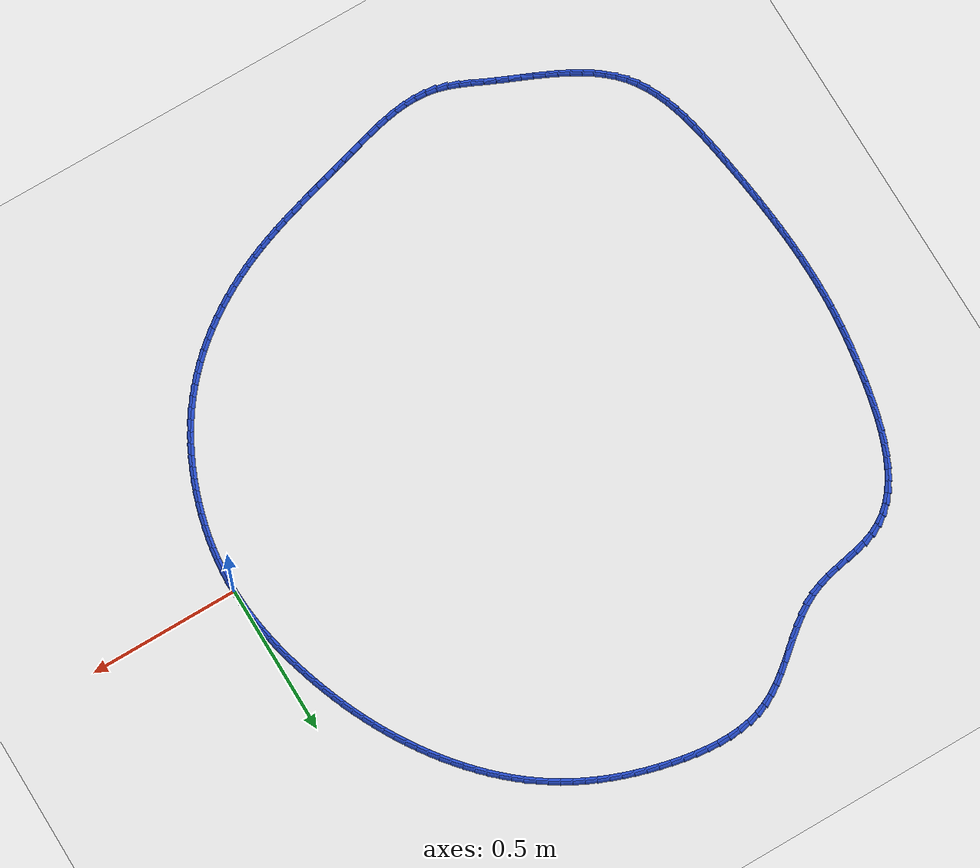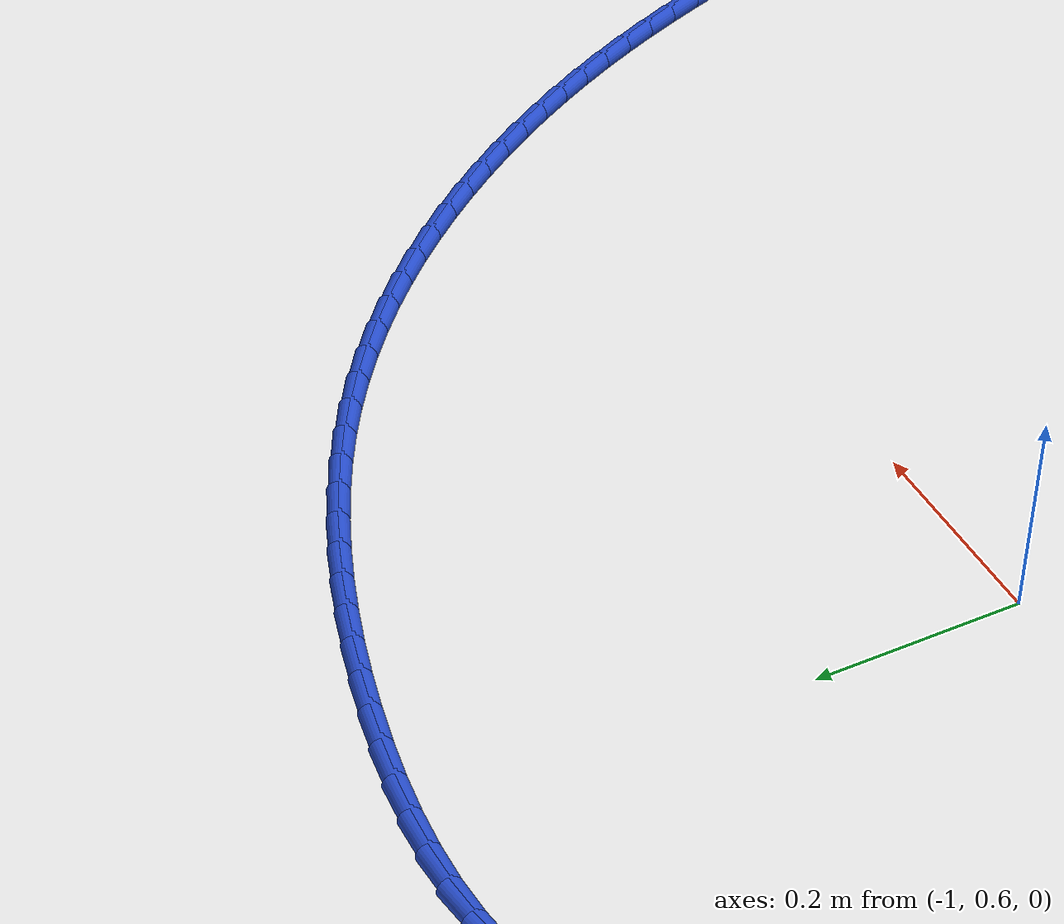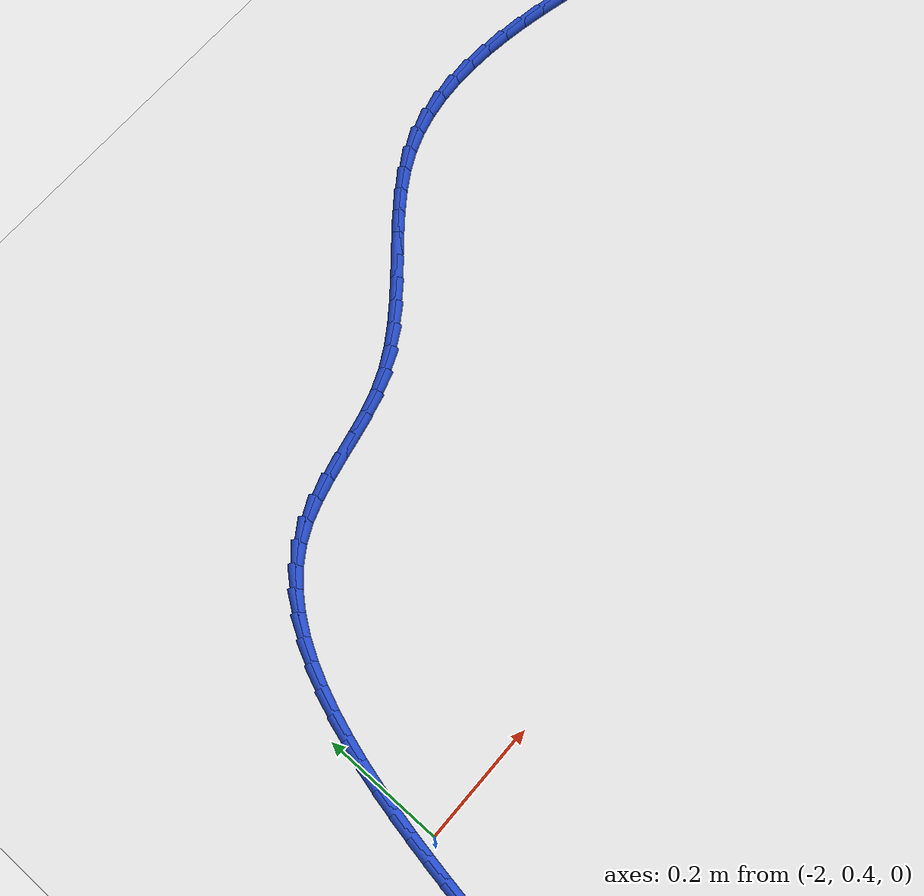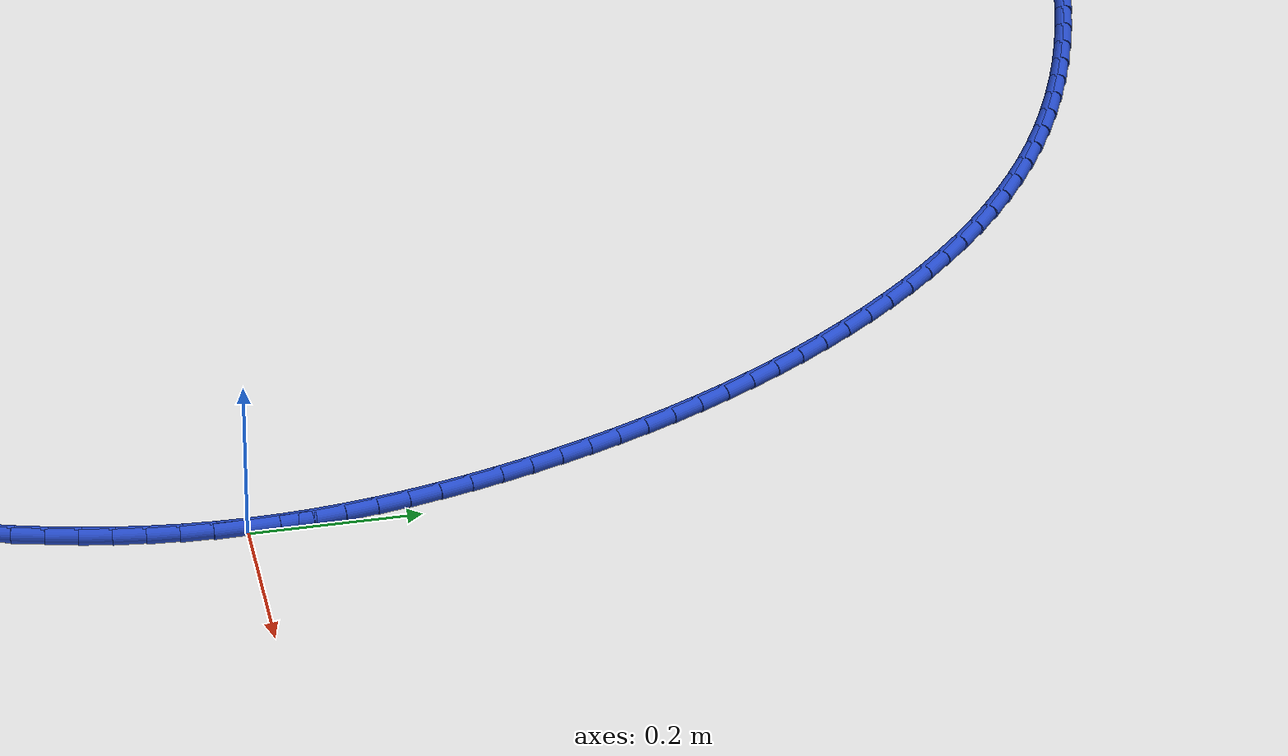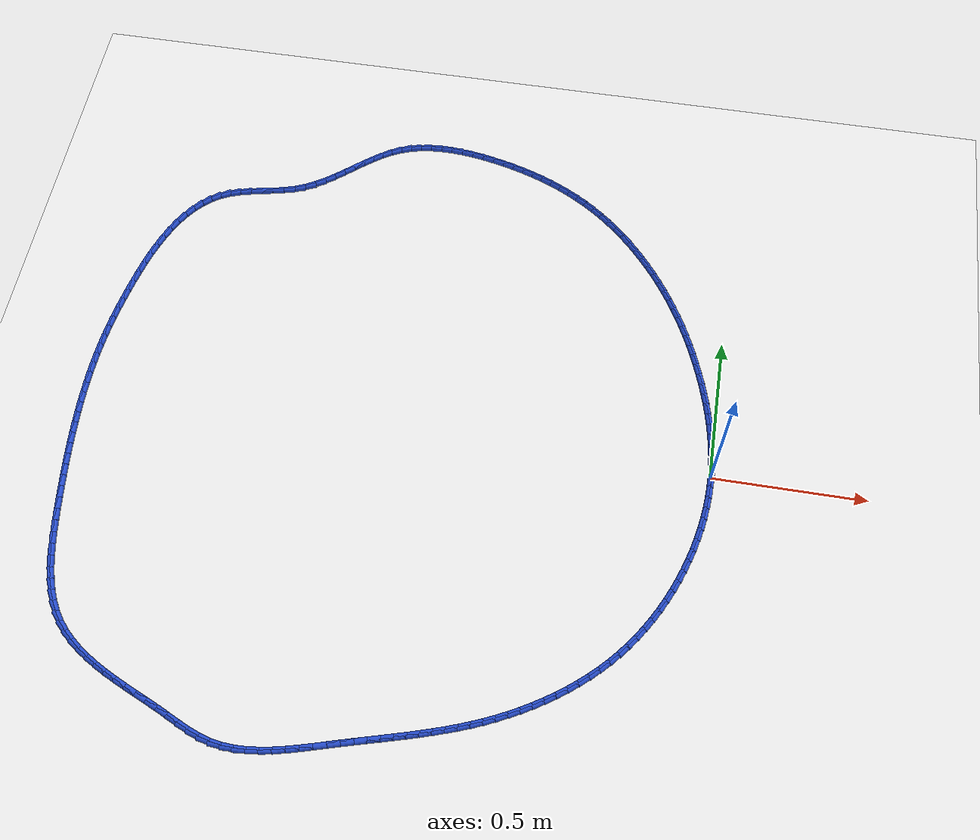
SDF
<sdf version="1.6">
 <world name="default">
  <light name="sun" type="directional">
   <pose>0 0 10 0 -0 0</pose>
   <diffuse>0.8 0.8 0.8 1</diffuse>
   <specular>0.2 0.2 0.2 1</specular>
   <attenuation>
    <range>1000</range>
    <constant>0.9</constant>
    <linear>0.01</linear>
    <quadratic>0.001</quadratic>
   </attenuation>
   <direction>-0.5 0.1 -0.9</direction>
  </light>
  <model name="ground_plane">
   <static>1</static>
   <link name="link">
    <collision name="collision">
     <geometry><plane><normal>0 0 1</normal><size>100 100</size></plane></geometry>
     <surface><friction><ode><mu>100</mu><mu2>50</mu2></ode></friction></surface>
    </collision>
    <visual name="visual">
     <cast_shadows>0</cast_shadows>
     <geometry><plane><normal>0 0 1</normal><size>100 100</size></plane></geometry>
     <material>
      <script><uri>file://media/materials/scripts/gazebo.material</uri><name>Gazebo/WhiteGlow</name></script>
     </material>
    </visual>
   </link>
  </model>
  <gravity>0 0 -9.8</gravity>
  <magnetic_field>6e-06 2.3e-05 -4.2e-05</magnetic_field>
  <atmosphere type="adiabatic"/>
  <physics name="default_physics" default="0" type="ode">
   <max_step_size>0.001</max_step_size>
   <real_time_factor>1</real_time_factor>
   <real_time_update_rate>1000</real_time_update_rate>
  </physics>
  <scene><ambient>0.4 0.4 0.4 1</ambient><background>0.7 0.7 0.7 1</background><shadows>1</shadows></scene>
  <spherical_coordinates>
   <surface_model>EARTH_WGS84</surface_model>
   <latitude_deg>0</latitude_deg>
   <longitude_deg>0</longitude_deg>
   <elevation>0</elevation>
   <heading_deg>0</heading_deg>
  </spherical_coordinates>
  <model name="line">
   <link name="link_0">
    <pose>-2.7755575615628914e-17 1.3877787807814457e-17 0.01 0 1.57 -1.5406374045841118</pose>
    <collision name="collision">
     <geometry><cylinder><radius>0.01</radius><length>0.08</length></cylinder></geometry>
    </collision>
    <visual name="visual">
     <material>
      <script><name>Gazebo/Blue</name><uri>file://media/materials/scripts/gazebo.material</uri></script>
     </material>
     <geometry><cylinder><radius>0.01</radius><length>0.08</length></cylinder></geometry>
    </visual>
   </link>
   <link name="link_1">
    <pose>-0.0011392396396819676 0.03776309406163166 0.01 0 1.57 -1.5000262374223226</pose>
    <collision name="collision">
     <geometry><cylinder><radius>0.01</radius><length>0.08</length></cylinder></geometry>
    </collision>
    <visual name="visual">
     <material>
      <script><name>Gazebo/Blue</name><uri>file://media/materials/scripts/gazebo.material</uri></script>
     </material>
     <geometry><cylinder><radius>0.01</radius><length>0.08</length></cylinder></geometry>
    </visual>
   </link>
   <link name="link_2">
    <pose>-0.0038113882761057626 0.07545820087612244 0.01 0 1.57 -1.4617151489560283</pose>
    <collision name="collision">
     <geometry><cylinder><radius>0.01</radius><length>0.08</length></cylinder></geometry>
    </collision>
    <visual name="visual">
     <material>
      <script><name>Gazebo/Blue</name><uri>file://media/materials/scripts/gazebo.material</uri></script>
     </material>
     <geometry><cylinder><radius>0.01</radius><length>0.08</length></cylinder></geometry>
    </visual>
   </link>
   <link name="link_3">
    <pose>-0.00792903573921639 0.11305683172591276 0.01 0 1.57 -1.425700947851287</pose>
    <collision name="collision">
     <geometry><cylinder><radius>0.01</radius><length>0.08</length></cylinder></geometry>
    </collision>
    <visual name="visual">
     <material>
      <script><name>Gazebo/Blue</name><uri>file://media/materials/scripts/gazebo.material</uri></script>
     </material>
     <geometry><cylinder><radius>0.01</radius><length>0.08</length></cylinder></geometry>
    </visual>
   </link>
   <link name="link_4">
    <pose>-0.01340477185895883 0.150530497893443 0.01 0 1.57 -1.3919566226149385</pose>
    <collision name="collision">
     <geometry><cylinder><radius>0.01</radius><length>0.08</length></cylinder></geometry>
    </collision>
    <visual name="visual">
     <material>
      <script><name>Gazebo/Blue</name><uri>file://media/materials/scripts/gazebo.material</uri></script>
     </material>
     <geometry><cylinder><radius>0.01</radius><length>0.08</length></cylinder></geometry>
    </visual>
   </link>
   <link name="link_5">
    <pose>-0.020151186465278047 0.18785071066115358 0.01 0 1.57 -1.36043728218958</pose>
    <collision name="collision">
     <geometry><cylinder><radius>0.01</radius><length>0.08</length></cylinder></geometry>
    </collision>
    <visual name="visual">
     <material>
      <script><name>Gazebo/Blue</name><uri>file://media/materials/scripts/gazebo.material</uri></script>
     </material>
     <geometry><cylinder><radius>0.01</radius><length>0.08</length></cylinder></geometry>
    </visual>
   </link>
   <link name="link_6">
    <pose>-0.028080869388119004 0.22498898131148481 0.01 0 1.57 -1.3310855227287415</pose>
    <collision name="collision">
     <geometry><cylinder><radius>0.01</radius><length>0.08</length></cylinder></geometry>
    </collision>
    <visual name="visual">
     <material>
      <script><name>Gazebo/Blue</name><uri>file://media/materials/scripts/gazebo.material</uri></script>
     </material>
     <geometry><cylinder><radius>0.01</radius><length>0.08</length></cylinder></geometry>
    </visual>
   </link>
   <link name="link_7">
    <pose>-0.0371064104574267 0.26191682112687725 0.01 0 1.57 -1.3038361089501525</pose>
    <collision name="collision">
     <geometry><cylinder><radius>0.01</radius><length>0.08</length></cylinder></geometry>
    </collision>
    <visual name="visual">
     <material>
      <script><name>Gazebo/Blue</name><uri>file://media/materials/scripts/gazebo.material</uri></script>
     </material>
     <geometry><cylinder><radius>0.01</radius><length>0.08</length></cylinder></geometry>
    </visual>
   </link>
   <link name="link_8">
    <pose>-0.047140399503146115 0.2986057413897713 0.01 0 1.57 -1.2786199484833694</pose>
    <collision name="collision">
     <geometry><cylinder><radius>0.01</radius><length>0.08</length></cylinder></geometry>
    </collision>
    <visual name="visual">
     <material>
      <script><name>Gazebo/Blue</name><uri>file://media/materials/scripts/gazebo.material</uri></script>
     </material>
     <geometry><cylinder><radius>0.01</radius><length>0.08</length></cylinder></geometry>
    </visual>
   </link>
   <link name="link_9">
    <pose>-0.058095426355222204 0.33502725338260736 0.01 0 1.57 -1.2551441013084685</pose>
    <collision name="collision">
     <geometry><cylinder><radius>0.01</radius><length>0.08</length></cylinder></geometry>
    </collision>
    <visual name="visual">
     <material>
      <script><name>Gazebo/Blue</name><uri>file://media/materials/scripts/gazebo.material</uri></script>
     </material>
     <geometry><cylinder><radius>0.01</radius><length>0.08</length></cylinder></geometry>
    </visual>
   </link>
   <link name="link_10">
    <pose>-0.06989311221895424 0.3711531897543148 0.01 0 1.57 -1.2317439700458501</pose>
    <collision name="collision">
     <geometry><cylinder><radius>0.01</radius><length>0.08</length></cylinder></geometry>
    </collision>
    <visual name="visual">
     <material>
      <script><name>Gazebo/Blue</name><uri>file://media/materials/scripts/gazebo.material</uri></script>
     </material>
     <geometry><cylinder><radius>0.01</radius><length>0.08</length></cylinder></geometry>
    </visual>
   </link>
   <link name="link_11">
    <pose>-0.08252032686424875 0.4069577049156046 0.01 0 1.57 -1.207695170480475</pose>
    <collision name="collision">
     <geometry><cylinder><radius>0.01</radius><length>0.08</length></cylinder></geometry>
    </collision>
    <visual name="visual">
     <material>
      <script><name>Gazebo/Blue</name><uri>file://media/materials/scripts/gazebo.material</uri></script>
     </material>
     <geometry><cylinder><radius>0.01</radius><length>0.08</length></cylinder></geometry>
    </visual>
   </link>
   <link name="link_12">
    <pose>-0.09599260824682476 0.4424159733869563 0.01 0 1.57 -1.1829866456857006</pose>
    <collision name="collision">
     <geometry><cylinder><radius>0.01</radius><length>0.08</length></cylinder></geometry>
    </collision>
    <visual name="visual">
     <material>
      <script><name>Gazebo/Blue</name><uri>file://media/materials/scripts/gazebo.material</uri></script>
     </material>
     <geometry><cylinder><radius>0.01</radius><length>0.08</length></cylinder></geometry>
    </visual>
   </link>
   <link name="link_13">
    <pose>-0.11032561764644747 0.47750317407713105 0.01 0 1.57 -1.1576131329335435</pose>
    <collision name="collision">
     <geometry><cylinder><radius>0.01</radius><length>0.08</length></cylinder></geometry>
    </collision>
    <visual name="visual">
     <material>
      <script><name>Gazebo/Blue</name><uri>file://media/materials/scripts/gazebo.material</uri></script>
     </material>
     <geometry><cylinder><radius>0.01</radius><length>0.08</length></cylinder></geometry>
    </visual>
   </link>
   <link name="link_14">
    <pose>-0.1255350163428818 0.5121944858948895 0.01 0 1.57 -1.1315724814242831</pose>
    <collision name="collision">
     <geometry><cylinder><radius>0.01</radius><length>0.08</length></cylinder></geometry>
    </collision>
    <visual name="visual">
     <material>
      <script><name>Gazebo/Blue</name><uri>file://media/materials/scripts/gazebo.material</uri></script>
     </material>
     <geometry><cylinder><radius>0.01</radius><length>0.08</length></cylinder></geometry>
    </visual>
   </link>
   <link name="link_15">
    <pose>-0.14163646561589296 0.5464650877489929 0.01 0 1.57 -1.1048660256667926</pose>
    <collision name="collision">
     <geometry><cylinder><radius>0.01</radius><length>0.08</length></cylinder></geometry>
    </collision>
    <visual name="visual">
     <material>
      <script><name>Gazebo/Blue</name><uri>file://media/materials/scripts/gazebo.material</uri></script>
     </material>
     <geometry><cylinder><radius>0.01</radius><length>0.08</length></cylinder></geometry>
    </visual>
   </link>
   <link name="link_16">
    <pose>-0.1586456267452459 0.5802901585482021 0.01 0 1.57 -1.0774989569841948</pose>
    <collision name="collision">
     <geometry><cylinder><radius>0.01</radius><length>0.08</length></cylinder></geometry>
    </collision>
    <visual name="visual">
     <material>
      <script><name>Gazebo/Blue</name><uri>file://media/materials/scripts/gazebo.material</uri></script>
     </material>
     <geometry><cylinder><radius>0.01</radius><length>0.08</length></cylinder></geometry>
    </visual>
   </link>
   <link name="link_17">
    <pose>-0.1765781610107057 0.6136448772012777 0.01 0 1.57 -1.0494806827380845</pose>
    <collision name="collision">
     <geometry><cylinder><radius>0.01</radius><length>0.08</length></cylinder></geometry>
    </collision>
    <visual name="visual">
     <material>
      <script><name>Gazebo/Blue</name><uri>file://media/materials/scripts/gazebo.material</uri></script>
     </material>
     <geometry><cylinder><radius>0.01</radius><length>0.08</length></cylinder></geometry>
    </visual>
   </link>
   <link name="link_18">
    <pose>-0.19544972969203764 0.6465044226169814 0.01 0 1.57 -1.0208251611801238</pose>
    <collision name="collision">
     <geometry><cylinder><radius>0.01</radius><length>0.08</length></cylinder></geometry>
    </collision>
    <visual name="visual">
     <material>
      <script><name>Gazebo/Blue</name><uri>file://media/materials/scripts/gazebo.material</uri></script>
     </material>
     <geometry><cylinder><radius>0.01</radius><length>0.08</length></cylinder></geometry>
    </visual>
   </link>
   <link name="link_19">
    <pose>-0.2152759940690065 0.6788439737040735 0.01 0 1.57 -0.9915511983826559</pose>
    <collision name="collision">
     <geometry><cylinder><radius>0.01</radius><length>0.08</length></cylinder></geometry>
    </collision>
    <visual name="visual">
     <material>
      <script><name>Gazebo/Blue</name><uri>file://media/materials/scripts/gazebo.material</uri></script>
     </material>
     <geometry><cylinder><radius>0.01</radius><length>0.08</length></cylinder></geometry>
    </visual>
   </link>
   <link name="link_20">
    <pose>-0.23607261542137753 0.7106387093713151 0.01 0 1.57 -0.9616801785968428</pose>
    <collision name="collision">
     <geometry><cylinder><radius>0.01</radius><length>0.08</length></cylinder></geometry>
    </collision>
    <visual name="visual">
     <material>
      <script><name>Gazebo/Blue</name><uri>file://media/materials/scripts/gazebo.material</uri></script>
     </material>
     <geometry><cylinder><radius>0.01</radius><length>0.08</length></cylinder></geometry>
    </visual>
   </link>
   <link name="link_21">
    <pose>-0.25785485416579945 0.7418630666074738 0.01 0 1.57 -0.9311301973567846</pose>
    <collision name="collision">
     <geometry><cylinder><radius>0.01</radius><length>0.08</length></cylinder></geometry>
    </collision>
    <visual name="visual">
     <material>
      <script><name>Gazebo/Blue</name><uri>file://media/materials/scripts/gazebo.material</uri></script>
     </material>
     <geometry><cylinder><radius>0.01</radius><length>0.08</length></cylinder></geometry>
    </visual>
   </link>
   <link name="link_22">
    <pose>-0.28062420440148644 0.7724660036138558 0.01 0 1.57 -0.899702229620366</pose>
    <collision name="collision">
     <geometry><cylinder><radius>0.01</radius><length>0.08</length></cylinder></geometry>
    </collision>
    <visual name="visual">
     <material>
      <script><name>Gazebo/Blue</name><uri>file://media/materials/scripts/gazebo.material</uri></script>
     </material>
     <geometry><cylinder><radius>0.01</radius><length>0.08</length></cylinder></geometry>
    </visual>
   </link>
   <link name="link_23">
    <pose>-0.3043652628468318 0.8023652048123683 0.01 0 1.57 -0.8672646880997724</pose>
    <collision name="collision">
     <geometry><cylinder><radius>0.01</radius><length>0.08</length></cylinder></geometry>
    </collision>
    <visual name="visual">
     <material>
      <script><name>Gazebo/Blue</name><uri>file://media/materials/scripts/gazebo.material</uri></script>
     </material>
     <geometry><cylinder><radius>0.01</radius><length>0.08</length></cylinder></geometry>
    </visual>
   </link>
   <link name="link_24">
    <pose>-0.3290615908885704 0.8314764384265299 0.01 0 1.57 -0.833693095139707</pose>
    <collision name="collision">
     <geometry><cylinder><radius>0.01</radius><length>0.08</length></cylinder></geometry>
    </collision>
    <visual name="visual">
     <material>
      <script><name>Gazebo/Blue</name><uri>file://media/materials/scripts/gazebo.material</uri></script>
     </material>
     <geometry><cylinder><radius>0.01</radius><length>0.08</length></cylinder></geometry>
    </visual>
   </link>
   <link name="link_25">
    <pose>-0.35469674991343736 0.8597154726798607 0.01 0 1.57 -0.7988640960731563</pose>
    <collision name="collision">
     <geometry><cylinder><radius>0.01</radius><length>0.08</length></cylinder></geometry>
    </collision>
    <visual name="visual">
     <material>
      <script><name>Gazebo/Blue</name><uri>file://media/materials/scripts/gazebo.material</uri></script>
     </material>
     <geometry><cylinder><radius>0.01</radius><length>0.08</length></cylinder></geometry>
    </visual>
   </link>
   <link name="link_26">
    <pose>-0.3812543013081674 0.8869980757958794 0.01 0 1.57 -0.7626564406219956</pose>
    <collision name="collision">
     <geometry><cylinder><radius>0.01</radius><length>0.08</length></cylinder></geometry>
    </collision>
    <visual name="visual">
     <material>
      <script><name>Gazebo/Blue</name><uri>file://media/materials/scripts/gazebo.material</uri></script>
     </material>
     <geometry><cylinder><radius>0.01</radius><length>0.08</length></cylinder></geometry>
    </visual>
   </link>
   <link name="link_27">
    <pose>-0.4087178064594955 0.9132400159981052 0.01 0 1.57 -0.7249525158089852</pose>
    <collision name="collision">
     <geometry><cylinder><radius>0.01</radius><length>0.08</length></cylinder></geometry>
    </collision>
    <visual name="visual">
     <material>
      <script><name>Gazebo/Blue</name><uri>file://media/materials/scripts/gazebo.material</uri></script>
     </material>
     <geometry><cylinder><radius>0.01</radius><length>0.08</length></cylinder></geometry>
    </visual>
   </link>
   <link name="link_28">
    <pose>-0.4370708267541571 0.9383570615100579 0.01 0 1.57 -0.6856405121485841</pose>
    <collision name="collision">
     <geometry><cylinder><radius>0.01</radius><length>0.08</length></cylinder></geometry>
    </collision>
    <visual name="visual">
     <material>
      <script><name>Gazebo/Blue</name><uri>file://media/materials/scripts/gazebo.material</uri></script>
     </material>
     <geometry><cylinder><radius>0.01</radius><length>0.08</length></cylinder></geometry>
    </visual>
   </link>
   <link name="link_29">
    <pose>-0.46629692357888675 0.9622649805552564 0.01 0 1.57 -0.644617300203668</pose>
    <collision name="collision">
     <geometry><cylinder><radius>0.01</radius><length>0.08</length></cylinder></geometry>
    </collision>
    <visual name="visual">
     <material>
      <script><name>Gazebo/Blue</name><uri>file://media/materials/scripts/gazebo.material</uri></script>
     </material>
     <geometry><cylinder><radius>0.01</radius><length>0.08</length></cylinder></geometry>
    </visual>
   </link>
   <link name="link_30">
    <pose>-0.4963796583204193 0.9848795413572198 0.01 0 1.57 -0.6018433490432572</pose>
    <collision name="collision">
     <geometry><cylinder><radius>0.01</radius><length>0.08</length></cylinder></geometry>
    </collision>
    <visual name="visual">
     <material>
      <script><name>Gazebo/Blue</name><uri>file://media/materials/scripts/gazebo.material</uri></script>
     </material>
     <geometry><cylinder><radius>0.01</radius><length>0.08</length></cylinder></geometry>
    </visual>
   </link>
   <link name="link_31">
    <pose>-0.5273025149291422 1.00611879237708 0.01 0 1.57 -0.5585616730761743</pose>
    <collision name="collision">
     <geometry><cylinder><radius>0.01</radius><length>0.08</length></cylinder></geometry>
    </collision>
    <visual name="visual">
     <material>
      <script><name>Gazebo/Blue</name><uri>file://media/materials/scripts/gazebo.material</uri></script>
     </material>
     <geometry><cylinder><radius>0.01</radius><length>0.08</length></cylinder></geometry>
    </visual>
   </link>
   <link name="link_32">
    <pose>-0.5590470523618666 1.025957466603241 0.01 0 1.57 -0.5162318859606077</pose>
    <collision name="collision">
     <geometry><cylinder><radius>0.01</radius><length>0.08</length></cylinder></geometry>
    </collision>
    <visual name="visual">
     <material>
      <script><name>Gazebo/Blue</name><uri>file://media/materials/scripts/gazebo.material</uri></script>
     </material>
     <geometry><cylinder><radius>0.01</radius><length>0.08</length></cylinder></geometry>
    </visual>
   </link>
   <link name="link_33">
    <pose>-0.5915928210370628 1.0444294416611333 0.01 0 1.57 -0.4750725879860018</pose>
    <collision name="collision">
     <geometry><cylinder><radius>0.01</radius><length>0.08</length></cylinder></geometry>
    </collision>
    <visual name="visual">
     <material>
      <script><name>Gazebo/Blue</name><uri>file://media/materials/scripts/gazebo.material</uri></script>
     </material>
     <geometry><cylinder><radius>0.01</radius><length>0.08</length></cylinder></geometry>
    </visual>
   </link>
   <link name="link_34">
    <pose>-0.6249192772184453 1.0615713677141614 0.01 0 1.57 -0.4352156582199583</pose>
    <collision name="collision">
     <geometry><cylinder><radius>0.01</radius><length>0.08</length></cylinder></geometry>
    </collision>
    <visual name="visual">
     <material>
      <script><name>Gazebo/Blue</name><uri>file://media/materials/scripts/gazebo.material</uri></script>
     </material>
     <geometry><cylinder><radius>0.01</radius><length>0.08</length></cylinder></geometry>
    </visual>
   </link>
   <link name="link_35">
    <pose>-0.65900587716973 1.0774198949257305 0.01 0 1.57 -0.39676788484185255</pose>
    <collision name="collision">
     <geometry><cylinder><radius>0.01</radius><length>0.08</length></cylinder></geometry>
    </collision>
    <visual name="visual">
     <material>
      <script><name>Gazebo/Blue</name><uri>file://media/materials/scripts/gazebo.material</uri></script>
     </material>
     <geometry><cylinder><radius>0.01</radius><length>0.08</length></cylinder></geometry>
    </visual>
   </link>
   <link name="link_36">
    <pose>-0.6938320771546317 1.0920116734592458 0.01 0 1.57 -0.3598113329010088</pose>
    <collision name="collision">
     <geometry><cylinder><radius>0.01</radius><length>0.08</length></cylinder></geometry>
    </collision>
    <visual name="visual">
     <material>
      <script><name>Gazebo/Blue</name><uri>file://media/materials/scripts/gazebo.material</uri></script>
     </material>
     <geometry><cylinder><radius>0.01</radius><length>0.08</length></cylinder></geometry>
    </visual>
   </link>
   <link name="link_37">
    <pose>-0.7293773334368651 1.1053833534781108 0.01 0 1.57 -0.3244045953468325</pose>
    <collision name="collision">
     <geometry><cylinder><radius>0.01</radius><length>0.08</length></cylinder></geometry>
    </collision>
    <visual name="visual">
     <material>
      <script><name>Gazebo/Blue</name><uri>file://media/materials/scripts/gazebo.material</uri></script>
     </material>
     <geometry><cylinder><radius>0.01</radius><length>0.08</length></cylinder></geometry>
    </visual>
   </link>
   <link name="link_38">
    <pose>-0.7656211022801452 1.1175715851457315 0.01 0 1.57 -0.2905847045669322</pose>
    <collision name="collision">
     <geometry><cylinder><radius>0.01</radius><length>0.08</length></cylinder></geometry>
    </collision>
    <visual name="visual">
     <material>
      <script><name>Gazebo/Blue</name><uri>file://media/materials/scripts/gazebo.material</uri></script>
     </material>
     <geometry><cylinder><radius>0.01</radius><length>0.08</length></cylinder></geometry>
    </visual>
   </link>
   <link name="link_39">
    <pose>-0.8025428399481878 1.1286130186255126 0.01 0 1.57 -0.2583694801472251</pose>
    <collision name="collision">
     <geometry><cylinder><radius>0.01</radius><length>0.08</length></cylinder></geometry>
    </collision>
    <visual name="visual">
     <material>
      <script><name>Gazebo/Blue</name><uri>file://media/materials/scripts/gazebo.material</uri></script>
     </material>
     <geometry><cylinder><radius>0.01</radius><length>0.08</length></cylinder></geometry>
    </visual>
   </link>
   <link name="link_40">
    <pose>-0.8401220027047072 1.138544304080858 0.01 0 1.57 -0.22775881668565162</pose>
    <collision name="collision">
     <geometry><cylinder><radius>0.01</radius><length>0.08</length></cylinder></geometry>
    </collision>
    <visual name="visual">
     <material>
      <script><name>Gazebo/Blue</name><uri>file://media/materials/scripts/gazebo.material</uri></script>
     </material>
     <geometry><cylinder><radius>0.01</radius><length>0.08</length></cylinder></geometry>
    </visual>
   </link>
   <link name="link_41">
    <pose>-0.8783380072982557 1.147402030504463 0.01 0 1.57 -0.19698736914476042</pose>
    <collision name="collision">
     <geometry><cylinder><radius>0.01</radius><length>0.08</length></cylinder></geometry>
    </collision>
    <visual name="visual">
     <material>
      <script><name>Gazebo/Blue</name><uri>file://media/materials/scripts/gazebo.material</uri></script>
     </material>
     <geometry><cylinder><radius>0.01</radius><length>0.08</length></cylinder></geometry>
    </visual>
   </link>
   <link name="link_42">
    <pose>-0.91711777531145 1.1551415227275803 0.01 0 1.57 -0.16056854131868153</pose>
    <collision name="collision">
     <geometry><cylinder><radius>0.01</radius><length>0.08</length></cylinder></geometry>
    </collision>
    <visual name="visual">
     <material>
      <script><name>Gazebo/Blue</name><uri>file://media/materials/scripts/gazebo.material</uri></script>
     </material>
     <geometry><cylinder><radius>0.01</radius><length>0.08</length></cylinder></geometry>
    </visual>
   </link>
   <link name="link_43">
    <pose>-0.9562322274633748 1.1614766113575048 0.01 0 1.57 -0.11683518389842502</pose>
    <collision name="collision">
     <geometry><cylinder><radius>0.01</radius><length>0.08</length></cylinder></geometry>
    </collision>
    <visual name="visual">
     <material>
      <script><name>Gazebo/Blue</name><uri>file://media/materials/scripts/gazebo.material</uri></script>
     </material>
     <geometry><cylinder><radius>0.01</radius><length>0.08</length></cylinder></geometry>
    </visual>
   </link>
   <link name="link_44">
    <pose>-0.9954234387250263 1.1660764728798085 0.01 0 1.57 -0.06486166840234169</pose>
    <collision name="collision">
     <geometry><cylinder><radius>0.01</radius><length>0.08</length></cylinder></geometry>
    </collision>
    <visual name="visual">
     <material>
      <script><name>Gazebo/Blue</name><uri>file://media/materials/scripts/gazebo.material</uri></script>
     </material>
     <geometry><cylinder><radius>0.01</radius><length>0.08</length></cylinder></geometry>
    </visual>
   </link>
   <link name="link_45">
    <pose>-1.0344334840674019 1.1686102837800652 0.01 0 1.57 -0.0035502411233002303</pose>
    <collision name="collision">
     <geometry><cylinder><radius>0.01</radius><length>0.08</length></cylinder></geometry>
    </collision>
    <visual name="visual">
     <material>
      <script><name>Gazebo/Blue</name><uri>file://media/materials/scripts/gazebo.material</uri></script>
     </material>
     <geometry><cylinder><radius>0.01</radius><length>0.08</length></cylinder></geometry>
    </visual>
   </link>
   <link name="link_46">
    <pose>-1.0730044384614992 1.1687472205438472 0.01 0 1.57 0.06829844971645511</pose>
    <collision name="collision">
     <geometry><cylinder><radius>0.01</radius><length>0.08</length></cylinder></geometry>
    </collision>
    <visual name="visual">
     <material>
      <script><name>Gazebo/Blue</name><uri>file://media/materials/scripts/gazebo.material</uri></script>
     </material>
     <geometry><cylinder><radius>0.01</radius><length>0.08</length></cylinder></geometry>
    </visual>
   </link>
   <link name="link_47">
    <pose>-1.1108783768783137 1.166156459656727 0.01 0 1.57 0.15184051075123225</pose>
    <collision name="collision">
     <geometry><cylinder><radius>0.01</radius><length>0.08</length></cylinder></geometry>
    </collision>
    <visual name="visual">
     <material>
      <script><name>Gazebo/Blue</name><uri>file://media/materials/scripts/gazebo.material</uri></script>
     </material>
     <geometry><cylinder><radius>0.01</radius><length>0.08</length></cylinder></geometry>
    </visual>
   </link>
   <link name="link_48">
    <pose>-1.1477973742888428 1.1605071776042777 0.01 0 1.57 0.24793115189143936</pose>
    <collision name="collision">
     <geometry><cylinder><radius>0.01</radius><length>0.08</length></cylinder></geometry>
    </collision>
    <visual name="visual">
     <material>
      <script><name>Gazebo/Blue</name><uri>file://media/materials/scripts/gazebo.material</uri></script>
     </material>
     <geometry><cylinder><radius>0.01</radius><length>0.08</length></cylinder></geometry>
    </visual>
   </link>
   <link name="link_49">
    <pose>-1.1835035056640846 1.1514685508720721 0.01 0 1.57 0.3567264596219374</pose>
    <collision name="collision">
     <geometry><cylinder><radius>0.01</radius><length>0.08</length></cylinder></geometry>
    </collision>
    <visual name="visual">
     <material>
      <script><name>Gazebo/Blue</name><uri>file://media/materials/scripts/gazebo.material</uri></script>
     </material>
     <geometry><cylinder><radius>0.01</radius><length>0.08</length></cylinder></geometry>
    </visual>
   </link>
   <link name="link_50">
    <pose>-1.2177389878769347 1.1387100101199863 0.01 0 1.57 0.4695098181031871</pose>
    <collision name="collision">
     <geometry><cylinder><radius>0.01</radius><length>0.08</length></cylinder></geometry>
    </collision>
    <visual name="visual">
     <material>
      <script><name>Gazebo/Blue</name><uri>file://media/materials/scripts/gazebo.material</uri></script>
     </material>
     <geometry><cylinder><radius>0.01</radius><length>0.08</length></cylinder></geometry>
    </visual>
   </link>
   <link name="link_51">
    <pose>-1.2503837736342907 1.1221476980645322 0.01 0 1.57 0.5623052165219564</pose>
    <collision name="collision">
     <geometry><cylinder><radius>0.01</radius><length>0.08</length></cylinder></geometry>
    </collision>
    <visual name="visual">
     <material>
      <script><name>Gazebo/Blue</name><uri>file://media/materials/scripts/gazebo.material</uri></script>
     </material>
     <geometry><cylinder><radius>0.01</radius><length>0.08</length></cylinder></geometry>
    </visual>
   </link>
   <link name="link_52">
    <pose>-1.2817127892395068 1.102405233069398 0.01 0 1.57 0.6308195380504196</pose>
    <collision name="collision">
     <geometry><cylinder><radius>0.01</radius><length>0.08</length></cylinder></geometry>
    </collision>
    <visual name="visual">
     <material>
      <script><name>Gazebo/Blue</name><uri>file://media/materials/scripts/gazebo.material</uri></script>
     </material>
     <geometry><cylinder><radius>0.01</radius><length>0.08</length></cylinder></geometry>
    </visual>
   </link>
   <link name="link_53">
    <pose>-1.312071316674275 1.0802322544007161 0.01 0 1.57 0.676117447491139</pose>
    <collision name="collision">
     <geometry><cylinder><radius>0.01</radius><length>0.08</length></cylinder></geometry>
    </collision>
    <visual name="visual">
     <material>
      <script><name>Gazebo/Blue</name><uri>file://media/materials/scripts/gazebo.material</uri></script>
     </material>
     <geometry><cylinder><radius>0.01</radius><length>0.08</length></cylinder></geometry>
    </visual>
   </link>
   <link name="link_54">
    <pose>-1.3418046379202897 1.056378401324617 0.01 0 1.57 0.6995397166441519</pose>
    <collision name="collision">
     <geometry><cylinder><radius>0.01</radius><length>0.08</length></cylinder></geometry>
    </collision>
    <visual name="visual">
     <material>
      <script><name>Gazebo/Blue</name><uri>file://media/materials/scripts/gazebo.material</uri></script>
     </material>
     <geometry><cylinder><radius>0.01</radius><length>0.08</length></cylinder></geometry>
    </visual>
   </link>
   <link name="link_55">
    <pose>-1.3712580349592447 1.0315933131072312 0.01 0 1.57 0.7020451840256093</pose>
    <collision name="collision">
     <geometry><cylinder><radius>0.01</radius><length>0.08</length></cylinder></geometry>
    </collision>
    <visual name="visual">
     <material>
      <script><name>Gazebo/Blue</name><uri>file://media/materials/scripts/gazebo.material</uri></script>
     </material>
     <geometry><cylinder><radius>0.01</radius><length>0.08</length></cylinder></geometry>
    </visual>
   </link>
   <link name="link_56">
    <pose>-1.4007767897728327 1.006626629014691 0.01 0 1.57 0.683944739497234</pose>
    <collision name="collision">
     <geometry><cylinder><radius>0.01</radius><length>0.08</length></cylinder></geometry>
    </collision>
    <visual name="visual">
     <material>
      <script><name>Gazebo/Blue</name><uri>file://media/materials/scripts/gazebo.material</uri></script>
     </material>
     <geometry><cylinder><radius>0.01</radius><length>0.08</length></cylinder></geometry>
    </visual>
   </link>
   <link name="link_57">
    <pose>-1.4307061843427482 0.9822279883131274 0.01 0 1.57 0.6448964484346191</pose>
    <collision name="collision">
     <geometry><cylinder><radius>0.01</radius><length>0.08</length></cylinder></geometry>
    </collision>
    <visual name="visual">
     <material>
      <script><name>Gazebo/Blue</name><uri>file://media/materials/scripts/gazebo.material</uri></script>
     </material>
     <geometry><cylinder><radius>0.01</radius><length>0.08</length></cylinder></geometry>
    </visual>
   </link>
   <link name="link_58">
    <pose>-1.4613915006506841 0.9591470302686711 0.01 0 1.57 0.5841293864301806</pose>
    <collision name="collision">
     <geometry><cylinder><radius>0.01</radius><length>0.08</length></cylinder></geometry>
    </collision>
    <visual name="visual">
     <material>
      <script><name>Gazebo/Blue</name><uri>file://media/materials/scripts/gazebo.material</uri></script>
     </material>
     <geometry><cylinder><radius>0.01</radius><length>0.08</length></cylinder></geometry>
    </visual>
   </link>
   <link name="link_59">
    <pose>-1.493178020678334 0.938133394147454 0.01 0 1.57 0.500958939303732</pose>
    <collision name="collision">
     <geometry><cylinder><radius>0.01</radius><length>0.08</length></cylinder></geometry>
    </collision>
    <visual name="visual">
     <material>
      <script><name>Gazebo/Blue</name><uri>file://media/materials/scripts/gazebo.material</uri></script>
     </material>
     <geometry><cylinder><radius>0.01</radius><length>0.08</length></cylinder></geometry>
    </visual>
   </link>
   <link name="link_60">
    <pose>-1.5264110264073911 0.9199367192156065 0.01 0 1.57 0.396356768364996</pose>
    <collision name="collision">
     <geometry><cylinder><radius>0.01</radius><length>0.08</length></cylinder></geometry>
    </collision>
    <visual name="visual">
     <material>
      <script><name>Gazebo/Blue</name><uri>file://media/materials/scripts/gazebo.material</uri></script>
     </material>
     <geometry><cylinder><radius>0.01</radius><length>0.08</length></cylinder></geometry>
    </visual>
   </link>
   <link name="link_61">
    <pose>-1.5614235335956679 0.9052837983302336 0.01 0 1.57 0.2966175268896997</pose>
    <collision name="collision">
     <geometry><cylinder><radius>0.01</radius><length>0.08</length></cylinder></geometry>
    </collision>
    <visual name="visual">
     <material>
      <script><name>Gazebo/Blue</name><uri>file://media/materials/scripts/gazebo.material</uri></script>
     </material>
     <geometry><cylinder><radius>0.01</radius><length>0.08</length></cylinder></geometry>
    </visual>
   </link>
   <link name="link_62">
    <pose>-1.5981038096124809 0.8940730599149108 0.01 0 1.57 0.2322920167530408</pose>
    <collision name="collision">
     <geometry><cylinder><radius>0.01</radius><length>0.08</length></cylinder></geometry>
    </collision>
    <visual name="visual">
     <material>
      <script><name>Gazebo/Blue</name><uri>file://media/materials/scripts/gazebo.material</uri></script>
     </material>
     <geometry><cylinder><radius>0.01</radius><length>0.08</length></cylinder></geometry>
    </visual>
   </link>
   <link name="link_63">
    <pose>-1.6357802918718656 0.8851602232215176 0.01 0 1.57 0.20327832543353014</pose>
    <collision name="collision">
     <geometry><cylinder><radius>0.01</radius><length>0.08</length></cylinder></geometry>
    </collision>
    <visual name="visual">
     <material>
      <script><name>Gazebo/Blue</name><uri>file://media/materials/scripts/gazebo.material</uri></script>
     </material>
     <geometry><cylinder><radius>0.01</radius><length>0.08</length></cylinder></geometry>
    </visual>
   </link>
   <link name="link_64">
    <pose>-1.673745752484389 0.8773345792254784 0.01 0 1.57 0.20863043023930025</pose>
    <collision name="collision">
     <geometry><cylinder><radius>0.01</radius><length>0.08</length></cylinder></geometry>
    </collision>
    <visual name="visual">
     <material>
      <script><name>Gazebo/Blue</name><uri>file://media/materials/scripts/gazebo.material</uri></script>
     </material>
     <geometry><cylinder><radius>0.01</radius><length>0.08</length></cylinder></geometry>
    </visual>
   </link>
   <link name="link_65">
    <pose>-1.7112929635606184 0.8693854189022184 0.01 0 1.57 0.2495718267902497</pose>
    <collision name="collision">
     <geometry><cylinder><radius>0.01</radius><length>0.08</length></cylinder></geometry>
    </collision>
    <visual name="visual">
     <material>
      <script><name>Gazebo/Blue</name><uri>file://media/materials/scripts/gazebo.material</uri></script>
     </material>
     <geometry><cylinder><radius>0.01</radius><length>0.08</length></cylinder></geometry>
    </visual>
   </link>
   <link name="link_66">
    <pose>-1.7477146972111215 0.8601020332271623 0.01 0 1.57 0.32950098253120236</pose>
    <collision name="collision">
     <geometry><cylinder><radius>0.01</radius><length>0.08</length></cylinder></geometry>
    </collision>
    <visual name="visual">
     <material>
      <script><name>Gazebo/Blue</name><uri>file://media/materials/scripts/gazebo.material</uri></script>
     </material>
     <geometry><cylinder><radius>0.01</radius><length>0.08</length></cylinder></geometry>
    </visual>
   </link>
   <link name="link_67">
    <pose>-1.7823037255464649 0.848273713175735 0.01 0 1.57 0.4520616141428894</pose>
    <collision name="collision">
     <geometry><cylinder><radius>0.01</radius><length>0.08</length></cylinder></geometry>
    </collision>
    <visual name="visual">
     <material>
      <script><name>Gazebo/Blue</name><uri>file://media/materials/scripts/gazebo.material</uri></script>
     </material>
     <geometry><cylinder><radius>0.01</radius><length>0.08</length></cylinder></geometry>
    </visual>
   </link>
   <link name="link_68">
    <pose>-1.814361763759925 0.8327063208543125 0.01 0 1.57 0.5968548320473388</pose>
    <collision name="collision">
     <geometry><cylinder><radius>0.01</radius><length>0.08</length></cylinder></geometry>
    </collision>
    <visual name="visual">
     <material>
      <script><name>Gazebo/Blue</name><uri>file://media/materials/scripts/gazebo.material</uri></script>
     </material>
     <geometry><cylinder><radius>0.01</radius><length>0.08</length></cylinder></geometry>
    </visual>
   </link>
   <link name="link_69">
    <pose>-1.843550098198648 0.812871987582124 0.01 0 1.57 0.7316030867968547</pose>
    <collision name="collision">
     <geometry><cylinder><radius>0.01</radius><length>0.08</length></cylinder></geometry>
    </collision>
    <visual name="visual">
     <material>
      <script><name>Gazebo/Blue</name><uri>file://media/materials/scripts/gazebo.material</uri></script>
     </material>
     <geometry><cylinder><radius>0.01</radius><length>0.08</length></cylinder></geometry>
    </visual>
   </link>
   <link name="link_70">
    <pose>-1.8700041194943762 0.7891213386429766 0.01 0 1.57 0.851172405851625</pose>
    <collision name="collision">
     <geometry><cylinder><radius>0.01</radius><length>0.08</length></cylinder></geometry>
    </collision>
    <visual name="visual">
     <material>
      <script><name>Gazebo/Blue</name><uri>file://media/materials/scripts/gazebo.material</uri></script>
     </material>
     <geometry><cylinder><radius>0.01</radius><length>0.08</length></cylinder></geometry>
    </visual>
   </link>
   <link name="link_71">
    <pose>-1.8938916184346726 0.7618650353554957 0.01 0 1.57 0.954720301512632</pose>
    <collision name="collision">
     <geometry><cylinder><radius>0.01</radius><length>0.08</length></cylinder></geometry>
    </collision>
    <visual name="visual">
     <material>
      <script><name>Gazebo/Blue</name><uri>file://media/materials/scripts/gazebo.material</uri></script>
     </material>
     <geometry><cylinder><radius>0.01</radius><length>0.08</length></cylinder></geometry>
    </visual>
   </link>
   <link name="link_72">
    <pose>-1.915380385807099 0.731513739038308 0.01 0 1.57 1.043014550861219</pose>
    <collision name="collision">
     <geometry><cylinder><radius>0.01</radius><length>0.08</length></cylinder></geometry>
    </collision>
    <visual name="visual">
     <material>
      <script><name>Gazebo/Blue</name><uri>file://media/materials/scripts/gazebo.material</uri></script>
     </material>
     <geometry><cylinder><radius>0.01</radius><length>0.08</length></cylinder></geometry>
    </visual>
   </link>
   <link name="link_73">
    <pose>-1.9346382123992183 0.6984781110100386 0.01 0 1.57 1.1176244868157734</pose>
    <collision name="collision">
     <geometry><cylinder><radius>0.01</radius><length>0.08</length></cylinder></geometry>
    </collision>
    <visual name="visual">
     <material>
      <script><name>Gazebo/Blue</name><uri>file://media/materials/scripts/gazebo.material</uri></script>
     </material>
     <geometry><cylinder><radius>0.01</radius><length>0.08</length></cylinder></geometry>
    </visual>
   </link>
   <link name="link_74">
    <pose>-1.9518328889985916 0.663168812589313 0.01 0 1.57 1.1803486239143872</pose>
    <collision name="collision">
     <geometry><cylinder><radius>0.01</radius><length>0.08</length></cylinder></geometry>
    </collision>
    <visual name="visual">
     <material>
      <script><name>Gazebo/Blue</name><uri>file://media/materials/scripts/gazebo.material</uri></script>
     </material>
     <geometry><cylinder><radius>0.01</radius><length>0.08</length></cylinder></geometry>
    </visual>
   </link>
   <link name="link_75">
    <pose>-1.9671322063927823 0.6259965050947585 0.01 0 1.57 1.232896841184195</pose>
    <collision name="collision">
     <geometry><cylinder><radius>0.01</radius><length>0.08</length></cylinder></geometry>
    </collision>
    <visual name="visual">
     <material>
      <script><name>Gazebo/Blue</name><uri>file://media/materials/scripts/gazebo.material</uri></script>
     </material>
     <geometry><cylinder><radius>0.01</radius><length>0.08</length></cylinder></geometry>
    </visual>
   </link>
   <link name="link_76">
    <pose>-1.9807039553693515 0.5873718498449996 0.01 0 1.57 1.2767495447201374</pose>
    <collision name="collision">
     <geometry><cylinder><radius>0.01</radius><length>0.08</length></cylinder></geometry>
    </collision>
    <visual name="visual">
     <material>
      <script><name>Gazebo/Blue</name><uri>file://media/materials/scripts/gazebo.material</uri></script>
     </material>
     <geometry><cylinder><radius>0.01</radius><length>0.08</length></cylinder></geometry>
    </visual>
   </link>
   <link name="link_77">
    <pose>-1.9927159267158623 0.5477055081586623 0.01 0 1.57 1.3131149060759828</pose>
    <collision name="collision">
     <geometry><cylinder><radius>0.01</radius><length>0.08</length></cylinder></geometry>
    </collision>
    <visual name="visual">
     <material>
      <script><name>Gazebo/Blue</name><uri>file://media/materials/scripts/gazebo.material</uri></script>
     </material>
     <geometry><cylinder><radius>0.01</radius><length>0.08</length></cylinder></geometry>
    </visual>
   </link>
   <link name="link_78">
    <pose>-2.0033359112198763 0.507408141354373 0.01 0 1.57 1.3429305500263078</pose>
    <collision name="collision">
     <geometry><cylinder><radius>0.01</radius><length>0.08</length></cylinder></geometry>
    </collision>
    <visual name="visual">
     <material>
      <script><name>Gazebo/Blue</name><uri>file://media/materials/scripts/gazebo.material</uri></script>
     </material>
     <geometry><cylinder><radius>0.01</radius><length>0.08</length></cylinder></geometry>
    </visual>
   </link>
   <link name="link_79">
    <pose>-2.0127316996689566 0.4668904107507575 0.01 0 1.57 1.3668787842963723</pose>
    <collision name="collision">
     <geometry><cylinder><radius>0.01</radius><length>0.08</length></cylinder></geometry>
    </collision>
    <visual name="visual">
     <material>
      <script><name>Gazebo/Blue</name><uri>file://media/materials/scripts/gazebo.material</uri></script>
     </material>
     <geometry><cylinder><radius>0.01</radius><length>0.08</length></cylinder></geometry>
    </visual>
   </link>
   <link name="link_80">
    <pose>-2.021071082850665 0.4265629776664411 0.01 0 1.57 1.3853984115390987</pose>
    <collision name="collision">
     <geometry><cylinder><radius>0.01</radius><length>0.08</length></cylinder></geometry>
    </collision>
    <visual name="visual">
     <material>
      <script><name>Gazebo/Blue</name><uri>file://media/materials/scripts/gazebo.material</uri></script>
     </material>
     <geometry><cylinder><radius>0.01</radius><length>0.08</length></cylinder></geometry>
    </visual>
   </link>
   <link name="link_81">
    <pose>-2.028521851531091 0.3868365033497588 0.01 0 1.57 1.3999150574991281</pose>
    <collision name="collision">
     <geometry><cylinder><radius>0.01</radius><length>0.08</length></cylinder></geometry>
    </collision>
    <visual name="visual">
     <material>
      <script><name>Gazebo/Blue</name><uri>file://media/materials/scripts/gazebo.material</uri></script>
     </material>
     <geometry><cylinder><radius>0.01</radius><length>0.08</length></cylinder></geometry>
    </visual>
   </link>
   <link name="link_82">
    <pose>-2.0352203910949385 0.3480188360722709 0.01 0 1.57 1.4152177218081117</pose>
    <collision name="collision">
     <geometry><cylinder><radius>0.01</radius><length>0.08</length></cylinder></geometry>
    </collision>
    <visual name="visual">
     <material>
      <script><name>Gazebo/Blue</name><uri>file://media/materials/scripts/gazebo.material</uri></script>
     </material>
     <geometry><cylinder><radius>0.01</radius><length>0.08</length></cylinder></geometry>
    </visual>
   </link>
   <link name="link_83">
    <pose>-2.041180770321427 0.3100173916394607 0.01 0 1.57 1.4323834085821854</pose>
    <collision name="collision">
     <geometry><cylinder><radius>0.01</radius><length>0.08</length></cylinder></geometry>
    </collision>
    <visual name="visual">
     <material>
      <script><name>Gazebo/Blue</name><uri>file://media/materials/scripts/gazebo.material</uri></script>
     </material>
     <geometry><cylinder><radius>0.01</radius><length>0.08</length></cylinder></geometry>
    </visual>
   </link>
   <link name="link_84">
    <pose>-2.0463872834441625 0.27264211180837145 0.01 0 1.57 1.4512542368026482</pose>
    <collision name="collision">
     <geometry><cylinder><radius>0.01</radius><length>0.08</length></cylinder></geometry>
    </collision>
    <visual name="visual">
     <material>
      <script><name>Gazebo/Blue</name><uri>file://media/materials/scripts/gazebo.material</uri></script>
     </material>
     <geometry><cylinder><radius>0.01</radius><length>0.08</length></cylinder></geometry>
    </visual>
   </link>
   <link name="link_85">
    <pose>-2.0508242246967514 0.2357029383360449 0.01 0 1.57 1.4716039217898549</pose>
    <collision name="collision">
     <geometry><cylinder><radius>0.01</radius><length>0.08</length></cylinder></geometry>
    </collision>
    <visual name="visual">
     <material>
      <script><name>Gazebo/Blue</name><uri>file://media/materials/scripts/gazebo.material</uri></script>
     </material>
     <geometry><cylinder><radius>0.01</radius><length>0.08</length></cylinder></geometry>
    </visual>
   </link>
   <link name="link_86">
    <pose>-2.0544758883127985 0.19900981297952416 0.01 0 1.57 1.4931350539523731</pose>
    <collision name="collision">
     <geometry><cylinder><radius>0.01</radius><length>0.08</length></cylinder></geometry>
    </collision>
    <visual name="visual">
     <material>
      <script><name>Gazebo/Blue</name><uri>file://media/materials/scripts/gazebo.material</uri></script>
     </material>
     <geometry><cylinder><radius>0.01</radius><length>0.08</length></cylinder></geometry>
    </visual>
   </link>
   <link name="link_87">
    <pose>-2.057326834351727 0.16237363619158257 0.01 0 1.57 1.5149298130749116</pose>
    <collision name="collision">
     <geometry><cylinder><radius>0.01</radius><length>0.08</length></cylinder></geometry>
    </collision>
    <visual name="visual">
     <material>
      <script><name>Gazebo/Blue</name><uri>file://media/materials/scripts/gazebo.material</uri></script>
     </material>
     <geometry><cylinder><radius>0.01</radius><length>0.08</length></cylinder></geometry>
    </visual>
   </link>
   <link name="link_88">
    <pose>-2.0593794889005794 0.12566974191192223 0.01 0 1.57 1.5358671797972034</pose>
    <collision name="collision">
     <geometry><cylinder><radius>0.01</radius><length>0.08</length></cylinder></geometry>
    </collision>
    <visual name="visual">
     <material>
      <script><name>Gazebo/Blue</name><uri>file://media/materials/scripts/gazebo.material</uri></script>
     </material>
     <geometry><cylinder><radius>0.01</radius><length>0.08</length></cylinder></geometry>
    </visual>
   </link>
   <link name="link_89">
    <pose>-2.06066513247328 0.08887752701900392 0.01 0 1.57 1.555820188643826</pose>
    <collision name="collision">
     <geometry><cylinder><radius>0.01</radius><length>0.08</length></cylinder></geometry>
    </collision>
    <visual name="visual">
     <material>
      <script><name>Gazebo/Blue</name><uri>file://media/materials/scripts/gazebo.material</uri></script>
     </material>
     <geometry><cylinder><radius>0.01</radius><length>0.08</length></cylinder></geometry>
    </visual>
   </link>
   <link name="link_90">
    <pose>-2.061217668657165 0.05198584845537807 0.01 0 1.57 -1.5668326027077852</pose>
    <collision name="collision">
     <geometry><cylinder><radius>0.01</radius><length>0.08</length></cylinder></geometry>
    </collision>
    <visual name="visual">
     <material>
      <script><name>Gazebo/Blue</name><uri>file://media/materials/scripts/gazebo.material</uri></script>
     </material>
     <geometry><cylinder><radius>0.01</radius><length>0.08</length></cylinder></geometry>
    </visual>
   </link>
   <link name="link_91">
    <pose>-2.061071001039571 0.014983563163595687 0.01 0 1.57 -1.5489280575588757</pose>
    <collision name="collision">
     <geometry><cylinder><radius>0.01</radius><length>0.08</length></cylinder></geometry>
    </collision>
    <visual name="visual">
     <material>
      <script><name>Gazebo/Blue</name><uri>file://media/materials/scripts/gazebo.material</uri></script>
     </material>
     <geometry><cylinder><radius>0.01</radius><length>0.08</length></cylinder></geometry>
    </visual>
   </link>
   <link name="link_92">
    <pose>-2.0602590332078345 -0.022140471913793133 0.01 0 1.57 -1.5320748568194251</pose>
    <collision name="collision">
     <geometry><cylinder><radius>0.01</radius><length>0.08</length></cylinder></geometry>
    </collision>
    <visual name="visual">
     <material>
      <script><name>Gazebo/Blue</name><uri>file://media/materials/scripts/gazebo.material</uri></script>
     </material>
     <geometry><cylinder><radius>0.01</radius><length>0.08</length></cylinder></geometry>
    </visual>
   </link>
   <link name="link_93">
    <pose>-2.058815668749292 -0.059397399834235955 0.01 0 1.57 -1.5162834128904807</pose>
    <collision name="collision">
     <geometry><cylinder><radius>0.01</radius><length>0.08</length></cylinder></geometry>
    </collision>
    <visual name="visual">
     <material>
      <script><name>Gazebo/Blue</name><uri>file://media/materials/scripts/gazebo.material</uri></script>
     </material>
     <geometry><cylinder><radius>0.01</radius><length>0.08</length></cylinder></geometry>
    </visual>
   </link>
   <link name="link_94">
    <pose>-2.0567748112512807 -0.09679836365518263 0.01 0 1.57 -1.5015590809598447</pose>
    <collision name="collision">
     <geometry><cylinder><radius>0.01</radius><length>0.08</length></cylinder></geometry>
    </collision>
    <visual name="visual">
     <material>
      <script><name>Gazebo/Blue</name><uri>file://media/materials/scripts/gazebo.material</uri></script>
     </material>
     <geometry><cylinder><radius>0.01</radius><length>0.08</length></cylinder></geometry>
    </visual>
   </link>
   <link name="link_95">
    <pose>-2.054170364301135 -0.13435450643408223 0.01 0 1.57 -1.4879027256521564</pose>
    <collision name="collision">
     <geometry><cylinder><radius>0.01</radius><length>0.08</length></cylinder></geometry>
    </collision>
    <visual name="visual">
     <material>
      <script><name>Gazebo/Blue</name><uri>file://media/materials/scripts/gazebo.material</uri></script>
     </material>
     <geometry><cylinder><radius>0.01</radius><length>0.08</length></cylinder></geometry>
    </visual>
   </link>
   <link name="link_96">
    <pose>-2.0510362314861927 -0.1720769712283839 0.01 0 1.57 -1.4753112795965233</pose>
    <collision name="collision">
     <geometry><cylinder><radius>0.01</radius><length>0.08</length></cylinder></geometry>
    </collision>
    <visual name="visual">
     <material>
      <script><name>Gazebo/Blue</name><uri>file://media/materials/scripts/gazebo.material</uri></script>
     </material>
     <geometry><cylinder><radius>0.01</radius><length>0.08</length></cylinder></geometry>
    </visual>
   </link>
   <link name="link_97">
    <pose>-2.0474063163937903 -0.2099769010955367 0.01 0 1.57 -1.4637782804214876</pose>
    <collision name="collision">
     <geometry><cylinder><radius>0.01</radius><length>0.08</length></cylinder></geometry>
    </collision>
    <visual name="visual">
     <material>
      <script><name>Gazebo/Blue</name><uri>file://media/materials/scripts/gazebo.material</uri></script>
     </material>
     <geometry><cylinder><radius>0.01</radius><length>0.08</length></cylinder></geometry>
    </visual>
   </link>
   <link name="link_98">
    <pose>-2.0433145226112637 -0.24806543909299056 0.01 0 1.57 -1.4532943760455075</pose>
    <collision name="collision">
     <geometry><cylinder><radius>0.01</radius><length>0.08</length></cylinder></geometry>
    </collision>
    <visual name="visual">
     <material>
      <script><name>Gazebo/Blue</name><uri>file://media/materials/scripts/gazebo.material</uri></script>
     </material>
     <geometry><cylinder><radius>0.01</radius><length>0.08</length></cylinder></geometry>
    </visual>
   </link>
   <link name="link_99">
    <pose>-2.0387947537259485 -0.28635372827819283 0.01 0 1.57 -1.443847791171324</pose>
    <collision name="collision">
     <geometry><cylinder><radius>0.01</radius><length>0.08</length></cylinder></geometry>
    </collision>
    <visual name="visual">
     <material>
      <script><name>Gazebo/Blue</name><uri>file://media/materials/scripts/gazebo.material</uri></script>
     </material>
     <geometry><cylinder><radius>0.01</radius><length>0.08</length></cylinder></geometry>
    </visual>
   </link>
   <link name="link_100">
    <pose>-2.033880913325183 -0.3248529117085936 0.01 0 1.57 -1.4354247505283497</pose>
    <collision name="collision">
     <geometry><cylinder><radius>0.01</radius><length>0.08</length></cylinder></geometry>
    </collision>
    <visual name="visual">
     <material>
      <script><name>Gazebo/Blue</name><uri>file://media/materials/scripts/gazebo.material</uri></script>
     </material>
     <geometry><cylinder><radius>0.01</radius><length>0.08</length></cylinder></geometry>
    </visual>
   </link>
   <link name="link_101">
    <pose>-2.028606904996302 -0.36357413244164183 0.01 0 1.57 -1.4280098566080592</pose>
    <collision name="collision">
     <geometry><cylinder><radius>0.01</radius><length>0.08</length></cylinder></geometry>
    </collision>
    <visual name="visual">
     <material>
      <script><name>Gazebo/Blue</name><uri>file://media/materials/scripts/gazebo.material</uri></script>
     </material>
     <geometry><cylinder><radius>0.01</radius><length>0.08</length></cylinder></geometry>
    </visual>
   </link>
   <link name="link_102">
    <pose>-2.023006632326643 -0.4025285335347868 0.01 0 1.57 -1.4215481683140312</pose>
    <collision name="collision">
     <geometry><cylinder><radius>0.01</radius><length>0.08</length></cylinder></geometry>
    </collision>
    <visual name="visual">
     <material>
      <script><name>Gazebo/Blue</name><uri>file://media/materials/scripts/gazebo.material</uri></script>
     </material>
     <geometry><cylinder><radius>0.01</radius><length>0.08</length></cylinder></geometry>
    </visual>
   </link>
   <link name="link_103">
    <pose>-2.017112656142543 -0.4417259904370665 0.01 0 1.57 -1.4130625610739236</pose>
    <collision name="collision">
     <geometry><cylinder><radius>0.01</radius><length>0.08</length></cylinder></geometry>
    </collision>
    <visual name="visual">
     <material>
      <script><name>Gazebo/Blue</name><uri>file://media/materials/scripts/gazebo.material</uri></script>
     </material>
     <geometry><cylinder><radius>0.01</radius><length>0.08</length></cylinder></geometry>
    </visual>
   </link>
   <link name="link_104">
    <pose>-2.0108534948650707 -0.4810781593103191 0.01 0 1.57 -1.3974720767289008</pose>
    <collision name="collision">
     <geometry><cylinder><radius>0.01</radius><length>0.08</length></cylinder></geometry>
    </collision>
    <visual name="visual">
     <material>
      <script><name>Gazebo/Blue</name><uri>file://media/materials/scripts/gazebo.material</uri></script>
     </material>
     <geometry><cylinder><radius>0.01</radius><length>0.08</length></cylinder></geometry>
    </visual>
   </link>
   <link name="link_105">
    <pose>-2.003981221558608 -0.5203301263767748 0.01 0 1.57 -1.3740370824486123</pose>
    <collision name="collision">
     <geometry><cylinder><radius>0.01</radius><length>0.08</length></cylinder></geometry>
    </collision>
    <visual name="visual">
     <material>
      <script><name>Gazebo/Blue</name><uri>file://media/materials/scripts/gazebo.material</uri></script>
     </material>
     <geometry><cylinder><radius>0.01</radius><length>0.08</length></cylinder></geometry>
    </visual>
   </link>
   <link name="link_106">
    <pose>-1.9962308070191077 -0.5592108327819497 0.01 0 1.57 -1.3422764441306183</pose>
    <collision name="collision">
     <geometry><cylinder><radius>0.01</radius><length>0.08</length></cylinder></geometry>
    </collision>
    <visual name="visual">
     <material>
      <script><name>Gazebo/Blue</name><uri>file://media/materials/scripts/gazebo.material</uri></script>
     </material>
     <geometry><cylinder><radius>0.01</radius><length>0.08</length></cylinder></geometry>
    </visual>
   </link>
   <link name="link_107">
    <pose>-1.9873372220425247 -0.5974492196713598 0.01 0 1.57 -1.30149861370294</pose>
    <collision name="collision">
     <geometry><cylinder><radius>0.01</radius><length>0.08</length></cylinder></geometry>
    </collision>
    <visual name="visual">
     <material>
      <script><name>Gazebo/Blue</name><uri>file://media/materials/scripts/gazebo.material</uri></script>
     </material>
     <geometry><cylinder><radius>0.01</radius><length>0.08</length></cylinder></geometry>
    </visual>
   </link>
   <link name="link_108">
    <pose>-1.977035437424811 -0.6347742281905209 0.01 0 1.57 -1.2508359429474907</pose>
    <collision name="collision">
     <geometry><cylinder><radius>0.01</radius><length>0.08</length></cylinder></geometry>
    </collision>
    <visual name="visual">
     <material>
      <script><name>Gazebo/Blue</name><uri>file://media/materials/scripts/gazebo.material</uri></script>
     </material>
     <geometry><cylinder><radius>0.01</radius><length>0.08</length></cylinder></geometry>
    </visual>
   </link>
   <link name="link_109">
    <pose>-1.9650604239619205 -0.6709147994849498 0.01 0 1.57 -1.189315017026701</pose>
    <collision name="collision">
     <geometry><cylinder><radius>0.01</radius><length>0.08</length></cylinder></geometry>
    </collision>
    <visual name="visual">
     <material>
      <script><name>Gazebo/Blue</name><uri>file://media/materials/scripts/gazebo.material</uri></script>
     </material>
     <geometry><cylinder><radius>0.01</radius><length>0.08</length></cylinder></geometry>
    </visual>
   </link>
   <link name="link_110">
    <pose>-1.9511471524498072 -0.7055998747001611 0.01 0 1.57 -1.1159912390308089</pose>
    <collision name="collision">
     <geometry><cylinder><radius>0.01</radius><length>0.08</length></cylinder></geometry>
    </collision>
    <visual name="visual">
     <material>
      <script><name>Gazebo/Blue</name><uri>file://media/materials/scripts/gazebo.material</uri></script>
     </material>
     <geometry><cylinder><radius>0.01</radius><length>0.08</length></cylinder></geometry>
    </visual>
   </link>
   <link name="link_111">
    <pose>-1.9350305936844232 -0.7385583949816711 0.01 0 1.57 -1.030178988380647</pose>
    <collision name="collision">
     <geometry><cylinder><radius>0.01</radius><length>0.08</length></cylinder></geometry>
    </collision>
    <visual name="visual">
     <material>
      <script><name>Gazebo/Blue</name><uri>file://media/materials/scripts/gazebo.material</uri></script>
     </material>
     <geometry><cylinder><radius>0.01</radius><length>0.08</length></cylinder></geometry>
    </visual>
   </link>
   <link name="link_112">
    <pose>-1.9164457184617238 -0.7695193014749965 0.01 0 1.57 -0.9318020281160496</pose>
    <collision name="collision">
     <geometry><cylinder><radius>0.01</radius><length>0.08</length></cylinder></geometry>
    </collision>
    <visual name="visual">
     <material>
      <script><name>Gazebo/Blue</name><uri>file://media/materials/scripts/gazebo.material</uri></script>
     </material>
     <geometry><cylinder><radius>0.01</radius><length>0.08</length></cylinder></geometry>
    </visual>
   </link>
   <link name="link_113">
    <pose>-1.8951277435496432 -0.7982117611974584 0.01 0 1.57 -0.8271094011224083</pose>
    <collision name="collision">
     <geometry><cylinder><radius>0.01</radius><length>0.08</length></cylinder></geometry>
    </collision>
    <visual name="visual">
     <material>
      <script><name>Gazebo/Blue</name><uri>file://media/materials/scripts/gazebo.material</uri></script>
     </material>
     <geometry><cylinder><radius>0.01</radius><length>0.08</length></cylinder></geometry>
    </visual>
   </link>
   <link name="link_114">
    <pose>-1.8709518797613696 -0.8244934952704042 0.01 0 1.57 -0.732105167405104</pose>
    <collision name="collision">
     <geometry><cylinder><radius>0.01</radius><length>0.08</length></cylinder></geometry>
    </collision>
    <visual name="visual">
     <material>
      <script><name>Gazebo/Blue</name><uri>file://media/materials/scripts/gazebo.material</uri></script>
     </material>
     <geometry><cylinder><radius>0.01</radius><length>0.08</length></cylinder></geometry>
    </visual>
   </link>
   <link name="link_115">
    <pose>-1.8441670763494065 -0.8485654223427613 0.01 0 1.57 -0.6502308630536964</pose>
    <collision name="collision">
     <geometry><cylinder><radius>0.01</radius><length>0.08</length></cylinder></geometry>
    </collision>
    <visual name="visual">
     <material>
      <script><name>Gazebo/Blue</name><uri>file://media/materials/scripts/gazebo.material</uri></script>
     </material>
     <geometry><cylinder><radius>0.01</radius><length>0.08</length></cylinder></geometry>
    </visual>
   </link>
   <link name="link_116">
    <pose>-1.8150839798027156 -0.8706851165657598 0.01 0 1.57 -0.5815401771580039</pose>
    <collision name="collision">
     <geometry><cylinder><radius>0.01</radius><length>0.08</length></cylinder></geometry>
    </collision>
    <visual name="visual">
     <material>
      <script><name>Gazebo/Blue</name><uri>file://media/materials/scripts/gazebo.material</uri></script>
     </material>
     <geometry><cylinder><radius>0.01</radius><length>0.08</length></cylinder></geometry>
    </visual>
   </link>
   <link name="link_117">
    <pose>-1.784013236610254 -0.8911101520906302 0.01 0 1.57 -0.5254526220353993</pose>
    <collision name="collision">
     <geometry><cylinder><radius>0.01</radius><length>0.08</length></cylinder></geometry>
    </collision>
    <visual name="visual">
     <material>
      <script><name>Gazebo/Blue</name><uri>file://media/materials/scripts/gazebo.material</uri></script>
     </material>
     <geometry><cylinder><radius>0.01</radius><length>0.08</length></cylinder></geometry>
    </visual>
   </link>
   <link name="link_118">
    <pose>-1.7512654932609806 -0.9100981030686028 0.01 0 1.57 -0.48111262671764476</pose>
    <collision name="collision">
     <geometry><cylinder><radius>0.01</radius><length>0.08</length></cylinder></geometry>
    </collision>
    <visual name="visual">
     <material>
      <script><name>Gazebo/Blue</name><uri>file://media/materials/scripts/gazebo.material</uri></script>
     </material>
     <geometry><cylinder><radius>0.01</radius><length>0.08</length></cylinder></geometry>
    </visual>
   </link>
   <link name="link_119">
    <pose>-1.7171513962438547 -0.927906543650908 0.01 0 1.57 -0.4476354757018459</pose>
    <collision name="collision">
     <geometry><cylinder><radius>0.01</radius><length>0.08</length></cylinder></geometry>
    </collision>
    <visual name="visual">
     <material>
      <script><name>Gazebo/Blue</name><uri>file://media/materials/scripts/gazebo.material</uri></script>
     </material>
     <geometry><cylinder><radius>0.01</radius><length>0.08</length></cylinder></geometry>
    </visual>
   </link>
   <link name="link_120">
    <pose>-1.681981592047834 -0.9447930479887763 0.01 0 1.57 -0.424252821097757</pose>
    <collision name="collision">
     <geometry><cylinder><radius>0.01</radius><length>0.08</length></cylinder></geometry>
    </collision>
    <visual name="visual">
     <material>
      <script><name>Gazebo/Blue</name><uri>file://media/materials/scripts/gazebo.material</uri></script>
     </material>
     <geometry><cylinder><radius>0.01</radius><length>0.08</length></cylinder></geometry>
    </visual>
   </link>
   <link name="link_121">
    <pose>-1.6460667271618794 -0.9610151902334376 0.01 0 1.57 -0.41038922094874863</pose>
    <collision name="collision">
     <geometry><cylinder><radius>0.01</radius><length>0.08</length></cylinder></geometry>
    </collision>
    <visual name="visual">
     <material>
      <script><name>Gazebo/Blue</name><uri>file://media/materials/scripts/gazebo.material</uri></script>
     </material>
     <geometry><cylinder><radius>0.01</radius><length>0.08</length></cylinder></geometry>
    </visual>
   </link>
   <link name="link_122">
    <pose>-1.6097174480749494 -0.9768305445361227 0.01 0 1.57 -0.4056983865834513</pose>
    <collision name="collision">
     <geometry><cylinder><radius>0.01</radius><length>0.08</length></cylinder></geometry>
    </collision>
    <visual name="visual">
     <material>
      <script><name>Gazebo/Blue</name><uri>file://media/materials/scripts/gazebo.material</uri></script>
     </material>
     <geometry><cylinder><radius>0.01</radius><length>0.08</length></cylinder></geometry>
    </visual>
   </link>
   <link name="link_123">
    <pose>-1.5732444012760016 -0.9924966850480615 0.01 0 1.57 -0.4100788079907987</pose>
    <collision name="collision">
     <geometry><cylinder><radius>0.01</radius><length>0.08</length></cylinder></geometry>
    </collision>
    <visual name="visual">
     <material>
      <script><name>Gazebo/Blue</name><uri>file://media/materials/scripts/gazebo.material</uri></script>
     </material>
     <geometry><cylinder><radius>0.01</radius><length>0.08</length></cylinder></geometry>
    </visual>
   </link>
   <link name="link_124">
    <pose>-1.5369582332539957 -1.0082711859204851 0.01 0 1.57 -0.42352882082982024</pose>
    <collision name="collision">
     <geometry><cylinder><radius>0.01</radius><length>0.08</length></cylinder></geometry>
    </collision>
    <visual name="visual">
     <material>
      <script><name>Gazebo/Blue</name><uri>file://media/materials/scripts/gazebo.material</uri></script>
     </material>
     <geometry><cylinder><radius>0.01</radius><length>0.08</length></cylinder></geometry>
    </visual>
   </link>
   <link name="link_125">
    <pose>-1.5011671329136251 -1.024406236558928 0.01 0 1.57 -0.4329900986601242</pose>
    <collision name="collision">
     <geometry><cylinder><radius>0.01</radius><length>0.08</length></cylinder></geometry>
    </collision>
    <visual name="visual">
     <material>
      <script><name>Gazebo/Blue</name><uri>file://media/materials/scripts/gazebo.material</uri></script>
     </material>
     <geometry><cylinder><radius>0.01</radius><length>0.08</length></cylinder></geometry>
    </visual>
   </link>
   <link name="link_126">
    <pose>-1.4659626421719958 -1.0406793370774634 0.01 0 1.57 -0.4142440083113537</pose>
    <collision name="collision">
     <geometry><cylinder><radius>0.01</radius><length>0.08</length></cylinder></geometry>
    </collision>
    <visual name="visual">
     <material>
      <script><name>Gazebo/Blue</name><uri>file://media/materials/scripts/gazebo.material</uri></script>
     </material>
     <geometry><cylinder><radius>0.01</radius><length>0.08</length></cylinder></geometry>
    </visual>
   </link>
   <link name="link_127">
    <pose>-1.4310531842679384 -1.0560285467284916 0.01 0 1.57 -0.3631058786709661</pose>
    <collision name="collision">
     <geometry><cylinder><radius>0.01</radius><length>0.08</length></cylinder></geometry>
    </collision>
    <visual name="visual">
     <material>
      <script><name>Gazebo/Blue</name><uri>file://media/materials/scripts/gazebo.material</uri></script>
     </material>
     <geometry><cylinder><radius>0.01</radius><length>0.08</length></cylinder></geometry>
    </visual>
   </link>
   <link name="link_128">
    <pose>-1.3961079994917922 -1.0693060720772252 0.01 0 1.57 -0.27748779551382485</pose>
    <collision name="collision">
     <geometry><cylinder><radius>0.01</radius><length>0.08</length></cylinder></geometry>
    </collision>
    <visual name="visual">
     <material>
      <script><name>Gazebo/Blue</name><uri>file://media/materials/scripts/gazebo.material</uri></script>
     </material>
     <geometry><cylinder><radius>0.01</radius><length>0.08</length></cylinder></geometry>
    </visual>
   </link>
   <link name="link_129">
    <pose>-1.3607963281361954 -1.079364119697607 0.01 0 1.57 -0.16453799445522496</pose>
    <collision name="collision">
     <geometry><cylinder><radius>0.01</radius><length>0.08</length></cylinder></geometry>
    </collision>
    <visual name="visual">
     <material>
      <script><name>Gazebo/Blue</name><uri>file://media/materials/scripts/gazebo.material</uri></script>
     </material>
     <geometry><cylinder><radius>0.01</radius><length>0.08</length></cylinder></geometry>
    </visual>
   </link>
   <link name="link_130">
    <pose>-1.324860098515279 -1.0853309383494893 0.01 0 1.57 -0.05735552575970793</pose>
    <collision name="collision">
     <geometry><cylinder><radius>0.01</radius><length>0.08</length></cylinder></geometry>
    </collision>
    <visual name="visual">
     <material>
      <script><name>Gazebo/Blue</name><uri>file://media/materials/scripts/gazebo.material</uri></script>
     </material>
     <geometry><cylinder><radius>0.01</radius><length>0.08</length></cylinder></geometry>
    </visual>
   </link>
   <link name="link_131">
    <pose>-1.2883292367247936 -1.0874284857085112 0.01 0 1.57 0.03452928628432661</pose>
    <collision name="collision">
     <geometry><cylinder><radius>0.01</radius><length>0.08</length></cylinder></geometry>
    </collision>
    <visual name="visual">
     <material>
      <script><name>Gazebo/Blue</name><uri>file://media/materials/scripts/gazebo.material</uri></script>
     </material>
     <geometry><cylinder><radius>0.01</radius><length>0.08</length></cylinder></geometry>
    </visual>
   </link>
   <link name="link_132">
    <pose>-1.2513049862402819 -1.0861495564466468 0.01 0 1.57 0.11079539597028687</pose>
    <collision name="collision">
     <geometry><cylinder><radius>0.01</radius><length>0.08</length></cylinder></geometry>
    </collision>
    <visual name="visual">
     <material>
      <script><name>Gazebo/Blue</name><uri>file://media/materials/scripts/gazebo.material</uri></script>
     </material>
     <geometry><cylinder><radius>0.01</radius><length>0.08</length></cylinder></geometry>
    </visual>
   </link>
   <link name="link_133">
    <pose>-1.2138885905372838 -1.0819869452358717 0.01 0 1.57 0.17208032031687223</pose>
    <collision name="collision">
     <geometry><cylinder><radius>0.01</radius><length>0.08</length></cylinder></geometry>
    </collision>
    <visual name="visual">
     <material>
      <script><name>Gazebo/Blue</name><uri>file://media/materials/scripts/gazebo.material</uri></script>
     </material>
     <geometry><cylinder><radius>0.01</radius><length>0.08</length></cylinder></geometry>
    </visual>
   </link>
   <link name="link_134">
    <pose>-1.1761812930913402 -1.0754334467481605 0.01 0 1.57 0.21942432757377883</pose>
    <collision name="collision">
     <geometry><cylinder><radius>0.01</radius><length>0.08</length></cylinder></geometry>
    </collision>
    <visual name="visual">
     <material>
      <script><name>Gazebo/Blue</name><uri>file://media/materials/scripts/gazebo.material</uri></script>
     </material>
     <geometry><cylinder><radius>0.01</radius><length>0.08</length></cylinder></geometry>
    </visual>
   </link>
   <link name="link_135">
    <pose>-1.1382843373779927 -1.0669818556554886 0.01 0 1.57 0.2538919012269848</pose>
    <collision name="collision">
     <geometry><cylinder><radius>0.01</radius><length>0.08</length></cylinder></geometry>
    </collision>
    <visual name="visual">
     <material>
      <script><name>Gazebo/Blue</name><uri>file://media/materials/scripts/gazebo.material</uri></script>
     </material>
     <geometry><cylinder><radius>0.01</radius><length>0.08</length></cylinder></geometry>
    </visual>
   </link>
   <link name="link_136">
    <pose>-1.100298966872782 -1.0571249666298308 0.01 0 1.57 0.27635310047939754</pose>
    <collision name="collision">
     <geometry><cylinder><radius>0.01</radius><length>0.08</length></cylinder></geometry>
    </collision>
    <visual name="visual">
     <material>
      <script><name>Gazebo/Blue</name><uri>file://media/materials/scripts/gazebo.material</uri></script>
     </material>
     <geometry><cylinder><radius>0.01</radius><length>0.08</length></cylinder></geometry>
    </visual>
   </link>
   <link name="link_137">
    <pose>-1.062326425051248 -1.0463555743431618 0.01 0 1.57 0.28736997491790855</pose>
    <collision name="collision">
     <geometry><cylinder><radius>0.01</radius><length>0.08</length></cylinder></geometry>
    </collision>
    <visual name="visual">
     <material>
      <script><name>Gazebo/Blue</name><uri>file://media/materials/scripts/gazebo.material</uri></script>
     </material>
     <geometry><cylinder><radius>0.01</radius><length>0.08</length></cylinder></geometry>
    </visual>
   </link>
   <link name="link_138">
    <pose>-1.0244679553889338 -1.0351664734674568 0.01 0 1.57 0.2871787783379912</pose>
    <collision name="collision">
     <geometry><cylinder><radius>0.01</radius><length>0.08</length></cylinder></geometry>
    </collision>
    <visual name="visual">
     <material>
      <script><name>Gazebo/Blue</name><uri>file://media/materials/scripts/gazebo.material</uri></script>
     </material>
     <geometry><cylinder><radius>0.01</radius><length>0.08</length></cylinder></geometry>
    </visual>
   </link>
   <link name="link_139">
    <pose>-0.9868245251299232 -1.0240487531974563 0.01 0 1.57 0.28033060979213975</pose>
    <collision name="collision">
     <geometry><cylinder><radius>0.01</radius><length>0.08</length></cylinder></geometry>
    </collision>
    <visual name="visual">
     <material>
      <script><name>Gazebo/Blue</name><uri>file://media/materials/scripts/gazebo.material</uri></script>
     </material>
     <geometry><cylinder><radius>0.01</radius><length>0.08</length></cylinder></geometry>
    </visual>
   </link>
   <link name="link_140">
    <pose>-0.9494645210804005 -1.0132923482467446 0.01 0 1.57 0.27583733616365835</pose>
    <collision name="collision">
     <geometry><cylinder><radius>0.01</radius><length>0.08</length></cylinder></geometry>
    </collision>
    <visual name="visual">
     <material>
      <script><name>Gazebo/Blue</name><uri>file://media/materials/scripts/gazebo.material</uri></script>
     </material>
     <geometry><cylinder><radius>0.01</radius><length>0.08</length></cylinder></geometry>
    </visual>
   </link>
   <link name="link_141">
    <pose>-0.9123935027045678 -1.0027992918090782 0.01 0 1.57 0.27483399132255487</pose>
    <collision name="collision">
     <geometry><cylinder><radius>0.01</radius><length>0.08</length></cylinder></geometry>
    </collision>
    <visual name="visual">
     <material>
      <script><name>Gazebo/Blue</name><uri>file://media/materials/scripts/gazebo.material</uri></script>
     </material>
     <geometry><cylinder><radius>0.01</radius><length>0.08</length></cylinder></geometry>
    </visual>
   </link>
   <link name="link_142">
    <pose>-0.8756098732380624 -0.9924274338954037 0.01 0 1.57 0.2774091949681765</pose>
    <collision name="collision">
     <geometry><cylinder><radius>0.01</radius><length>0.08</length></cylinder></geometry>
    </collision>
    <visual name="visual">
     <material>
      <script><name>Gazebo/Blue</name><uri>file://media/materials/scripts/gazebo.material</uri></script>
     </material>
     <geometry><cylinder><radius>0.01</radius><length>0.08</length></cylinder></geometry>
    </visual>
   </link>
   <link name="link_143">
    <pose>-0.8391120359165241 -0.9820346245166693 0.01 0 1.57 0.2836311924141654</pose>
    <collision name="collision">
     <geometry><cylinder><radius>0.01</radius><length>0.08</length></cylinder></geometry>
    </collision>
    <visual name="visual">
     <material>
      <script><name>Gazebo/Blue</name><uri>file://media/materials/scripts/gazebo.material</uri></script>
     </material>
     <geometry><cylinder><radius>0.01</radius><length>0.08</length></cylinder></geometry>
    </visual>
   </link>
   <link name="link_144">
    <pose>-0.8028983939755909 -0.9714787136838232 0.01 0 1.57 0.29354534843088353</pose>
    <collision name="collision">
     <geometry><cylinder><radius>0.01</radius><length>0.08</length></cylinder></geometry>
    </collision>
    <visual name="visual">
     <material>
      <script><name>Gazebo/Blue</name><uri>file://media/materials/scripts/gazebo.material</uri></script>
     </material>
     <geometry><cylinder><radius>0.01</radius><length>0.08</length></cylinder></geometry>
    </visual>
   </link>
   <link name="link_145">
    <pose>-0.7669673506509007 -0.9606175514078121 0.01 0 1.57 0.3071704149923046</pose>
    <collision name="collision">
     <geometry><cylinder><radius>0.01</radius><length>0.08</length></cylinder></geometry>
    </collision>
    <visual name="visual">
     <material>
      <script><name>Gazebo/Blue</name><uri>file://media/materials/scripts/gazebo.material</uri></script>
     </material>
     <geometry><cylinder><radius>0.01</radius><length>0.08</length></cylinder></geometry>
    </visual>
   </link>
   <link name="link_146">
    <pose>-0.7313173091780921 -0.9493089876995844 0.01 0 1.57 0.32449361112644076</pose>
    <collision name="collision">
     <geometry><cylinder><radius>0.01</radius><length>0.08</length></cylinder></geometry>
    </collision>
    <visual name="visual">
     <material>
      <script><name>Gazebo/Blue</name><uri>file://media/materials/scripts/gazebo.material</uri></script>
     </material>
     <geometry><cylinder><radius>0.01</radius><length>0.08</length></cylinder></geometry>
    </visual>
   </link>
   <link name="link_147">
    <pose>-0.6959466727928035 -0.9374108725700878 0.01 0 1.57 0.3454647228033851</pose>
    <collision name="collision">
     <geometry><cylinder><radius>0.01</radius><length>0.08</length></cylinder></geometry>
    </collision>
    <visual name="visual">
     <material>
      <script><name>Gazebo/Blue</name><uri>file://media/materials/scripts/gazebo.material</uri></script>
     </material>
     <geometry><cylinder><radius>0.01</radius><length>0.08</length></cylinder></geometry>
    </visual>
   </link>
   <link name="link_148">
    <pose>-0.6608538447306723 -0.9247810560302692 0.01 0 1.57 0.3699896386387592</pose>
    <collision name="collision">
     <geometry><cylinder><radius>0.01</radius><length>0.08</length></cylinder></geometry>
    </collision>
    <visual name="visual">
     <material>
      <script><name>Gazebo/Blue</name><uri>file://media/materials/scripts/gazebo.material</uri></script>
     </material>
     <geometry><cylinder><radius>0.01</radius><length>0.08</length></cylinder></geometry>
    </visual>
   </link>
   <link name="link_149">
    <pose>-0.6260372282273385 -0.9112773880910778 0.01 0 1.57 0.39792396917316925</pose>
    <collision name="collision">
     <geometry><cylinder><radius>0.01</radius><length>0.08</length></cylinder></geometry>
    </collision>
    <visual name="visual">
     <material>
      <script><name>Gazebo/Blue</name><uri>file://media/materials/scripts/gazebo.material</uri></script>
     </material>
     <geometry><cylinder><radius>0.01</radius><length>0.08</length></cylinder></geometry>
    </visual>
   </link>
   <link name="link_150">
    <pose>-0.5914952265184393 -0.8967577187634599 0.01 0 1.57 0.4288684942451355</pose>
    <collision name="collision">
     <geometry><cylinder><radius>0.01</radius><length>0.08</length></cylinder></geometry>
    </collision>
    <visual name="visual">
     <material>
      <script><name>Gazebo/Blue</name><uri>file://media/materials/scripts/gazebo.material</uri></script>
     </material>
     <geometry><cylinder><radius>0.01</radius><length>0.08</length></cylinder></geometry>
    </visual>
   </link>
   <link name="link_151">
    <pose>-0.557234073786241 -0.8810917301310645 0.01 0 1.57 0.4611441816226867</pose>
    <collision name="collision">
     <geometry><cylinder><radius>0.01</radius><length>0.08</length></cylinder></geometry>
    </collision>
    <visual name="visual">
     <material>
      <script><name>Gazebo/Blue</name><uri>file://media/materials/scripts/gazebo.material</uri></script>
     </material>
     <geometry><cylinder><radius>0.01</radius><length>0.08</length></cylinder></geometry>
    </visual>
   </link>
   <link name="link_152">
    <pose>-0.5233209204410054 -0.8642411449046276 0.01 0 1.57 0.49413402091840103</pose>
    <collision name="collision">
     <geometry><cylinder><radius>0.01</radius><length>0.08</length></cylinder></geometry>
    </collision>
    <visual name="visual">
     <material>
      <script><name>Gazebo/Blue</name><uri>file://media/materials/scripts/gazebo.material</uri></script>
     </material>
     <geometry><cylinder><radius>0.01</radius><length>0.08</length></cylinder></geometry>
    </visual>
   </link>
   <link name="link_153">
    <pose>-0.489851456651081 -0.8462108075921084 0.01 0 1.57 0.5279810407179869</pose>
    <collision name="collision">
     <geometry><cylinder><radius>0.01</radius><length>0.08</length></cylinder></geometry>
    </collision>
    <visual name="visual">
     <material>
      <script><name>Gazebo/Blue</name><uri>file://media/materials/scripts/gazebo.material</uri></script>
     </material>
     <geometry><cylinder><radius>0.01</radius><length>0.08</length></cylinder></geometry>
    </visual>
   </link>
   <link name="link_154">
    <pose>-0.45692153594371276 -0.8270058095265866 0.01 0 1.57 0.5628297081690211</pose>
    <collision name="collision">
     <geometry><cylinder><radius>0.01</radius><length>0.08</length></cylinder></geometry>
    </collision>
    <visual name="visual">
     <material>
      <script><name>Gazebo/Blue</name><uri>file://media/materials/scripts/gazebo.material</uri></script>
     </material>
     <geometry><cylinder><radius>0.01</radius><length>0.08</length></cylinder></geometry>
    </visual>
   </link>
   <link name="link_155">
    <pose>-0.42462701184614815 -0.8066312420411432 0.01 0 1.57 0.5988217457042266</pose>
    <collision name="collision">
     <geometry><cylinder><radius>0.01</radius><length>0.08</length></cylinder></geometry>
    </collision>
    <visual name="visual">
     <material>
      <script><name>Gazebo/Blue</name><uri>file://media/materials/scripts/gazebo.material</uri></script>
     </material>
     <geometry><cylinder><radius>0.01</radius><length>0.08</length></cylinder></geometry>
    </visual>
   </link>
   <link name="link_156">
    <pose>-0.3930637378856324 -0.7850921964688586 0.01 0 1.57 0.6360955608301228</pose>
    <collision name="collision">
     <geometry><cylinder><radius>0.01</radius><length>0.08</length></cylinder></geometry>
    </collision>
    <visual name="visual">
     <material>
      <script><name>Gazebo/Blue</name><uri>file://media/materials/scripts/gazebo.material</uri></script>
     </material>
     <geometry><cylinder><radius>0.01</radius><length>0.08</length></cylinder></geometry>
    </visual>
   </link>
   <link name="link_157">
    <pose>-0.3623275675894113 -0.7623937641428126 0.01 0 1.57 0.6747850621855289</pose>
    <collision name="collision">
     <geometry><cylinder><radius>0.01</radius><length>0.08</length></cylinder></geometry>
    </collision>
    <visual name="visual">
     <material>
      <script><name>Gazebo/Blue</name><uri>file://media/materials/scripts/gazebo.material</uri></script>
     </material>
     <geometry><cylinder><radius>0.01</radius><length>0.08</length></cylinder></geometry>
    </visual>
   </link>
   <link name="link_158">
    <pose>-0.3325143544847307 -0.7385410363960851 0.01 0 1.57 0.715017780324634</pose>
    <collision name="collision">
     <geometry><cylinder><radius>0.01</radius><length>0.08</length></cylinder></geometry>
    </collision>
    <visual name="visual">
     <material>
      <script><name>Gazebo/Blue</name><uri>file://media/materials/scripts/gazebo.material</uri></script>
     </material>
     <geometry><cylinder><radius>0.01</radius><length>0.08</length></cylinder></geometry>
    </visual>
   </link>
   <link name="link_159">
    <pose>-0.30371995209883595 -0.7135391045617568 0.01 0 1.57 0.7569122108937019</pose>
    <collision name="collision">
     <geometry><cylinder><radius>0.01</radius><length>0.08</length></cylinder></geometry>
    </collision>
    <visual name="visual">
     <material>
      <script><name>Gazebo/Blue</name><uri>file://media/materials/scripts/gazebo.material</uri></script>
     </material>
     <geometry><cylinder><radius>0.01</radius><length>0.08</length></cylinder></geometry>
    </visual>
   </link>
   <link name="link_160">
    <pose>-0.27604021395897393 -0.6873930599729082 0.01 0 1.57 0.8005743114550423</pose>
    <collision name="collision">
     <geometry><cylinder><radius>0.01</radius><length>0.08</length></cylinder></geometry>
    </collision>
    <visual name="visual">
     <material>
      <script><name>Gazebo/Blue</name><uri>file://media/materials/scripts/gazebo.material</uri></script>
     </material>
     <geometry><cylinder><radius>0.01</radius><length>0.08</length></cylinder></geometry>
    </visual>
   </link>
   <link name="link_161">
    <pose>-0.24957099359239007 -0.6601079939626193 0.01 0 1.57 0.846061610735195</pose>
    <collision name="collision">
     <geometry><cylinder><radius>0.01</radius><length>0.08</length></cylinder></geometry>
    </collision>
    <visual name="visual">
     <material>
      <script><name>Gazebo/Blue</name><uri>file://media/materials/scripts/gazebo.material</uri></script>
     </material>
     <geometry><cylinder><radius>0.01</radius><length>0.08</length></cylinder></geometry>
    </visual>
   </link>
   <link name="link_162">
    <pose>-0.22440712301026502 -0.6316896482283683 0.01 0 1.57 0.8920964146522106</pose>
    <collision name="collision">
     <geometry><cylinder><radius>0.01</radius><length>0.08</length></cylinder></geometry>
    </collision>
    <visual name="visual">
     <material>
      <script><name>Gazebo/Blue</name><uri>file://media/materials/scripts/gazebo.material</uri></script>
     </material>
     <geometry><cylinder><radius>0.01</radius><length>0.08</length></cylinder></geometry>
    </visual>
   </link>
   <link name="link_163">
    <pose>-0.20060018183539585 -0.6021713017863936 0.01 0 1.57 0.9368789840097427</pose>
    <collision name="collision">
     <geometry><cylinder><radius>0.01</radius><length>0.08</length></cylinder></geometry>
    </collision>
    <visual name="visual">
     <material>
      <script><name>Gazebo/Blue</name><uri>file://media/materials/scripts/gazebo.material</uri></script>
     </material>
     <geometry><cylinder><radius>0.01</radius><length>0.08</length></cylinder></geometry>
    </visual>
   </link>
   <link name="link_164">
    <pose>-0.17814342441257877 -0.5716233673658293 0.01 0 1.57 0.9802829245117517</pose>
    <collision name="collision">
     <geometry><cylinder><radius>0.01</radius><length>0.08</length></cylinder></geometry>
    </collision>
    <visual name="visual">
     <material>
      <script><name>Gazebo/Blue</name><uri>file://media/materials/scripts/gazebo.material</uri></script>
     </material>
     <geometry><cylinder><radius>0.01</radius><length>0.08</length></cylinder></geometry>
    </visual>
   </link>
   <link name="link_165">
    <pose>-0.15702598426464665 -0.540118881282439 0.01 0 1.57 1.022329615112552</pose>
    <collision name="collision">
     <geometry><cylinder><radius>0.01</radius><length>0.08</length></cylinder></geometry>
    </collision>
    <visual name="visual">
     <material>
      <script><name>Gazebo/Blue</name><uri>file://media/materials/scripts/gazebo.material</uri></script>
     </material>
     <geometry><cylinder><radius>0.01</radius><length>0.08</length></cylinder></geometry>
    </visual>
   </link>
   <link name="link_166">
    <pose>-0.13723699491443364 -0.5077308798519887 0.01 0 1.57 1.0630580494791013</pose>
    <collision name="collision">
     <geometry><cylinder><radius>0.01</radius><length>0.08</length></cylinder></geometry>
    </collision>
    <visual name="visual">
     <material>
      <script><name>Gazebo/Blue</name><uri>file://media/materials/scripts/gazebo.material</uri></script>
     </material>
     <geometry><cylinder><radius>0.01</radius><length>0.08</length></cylinder></geometry>
    </visual>
   </link>
   <link name="link_167">
    <pose>-0.11876558988477265 -0.4745323993902425 0.01 0 1.57 1.1025219018681045</pose>
    <collision name="collision">
     <geometry><cylinder><radius>0.01</radius><length>0.08</length></cylinder></geometry>
    </collision>
    <visual name="visual">
     <material>
      <script><name>Gazebo/Blue</name><uri>file://media/materials/scripts/gazebo.material</uri></script>
     </material>
     <geometry><cylinder><radius>0.01</radius><length>0.08</length></cylinder></geometry>
    </visual>
   </link>
   <link name="link_168">
    <pose>-0.1016009026984971 -0.44059647621296516 0.01 0 1.57 1.140786840777429</pose>
    <collision name="collision">
     <geometry><cylinder><radius>0.01</radius><length>0.08</length></cylinder></geometry>
    </collision>
    <visual name="visual">
     <material>
      <script><name>Gazebo/Blue</name><uri>file://media/materials/scripts/gazebo.material</uri></script>
     </material>
     <geometry><cylinder><radius>0.01</radius><length>0.08</length></cylinder></geometry>
    </visual>
   </link>
   <link name="link_169">
    <pose>-0.08573206687844032 -0.40599614663592115 0.01 0 1.57 1.177928163824066</pose>
    <collision name="collision">
     <geometry><cylinder><radius>0.01</radius><length>0.08</length></cylinder></geometry>
    </collision>
    <visual name="visual">
     <material>
      <script><name>Gazebo/Blue</name><uri>file://media/materials/scripts/gazebo.material</uri></script>
     </material>
     <geometry><cylinder><radius>0.01</radius><length>0.08</length></cylinder></geometry>
    </visual>
   </link>
   <link name="link_170">
    <pose>-0.07114821594743537 -0.3708044469748745 0.01 0 1.57 1.2140304515697105</pose>
    <collision name="collision">
     <geometry><cylinder><radius>0.01</radius><length>0.08</length></cylinder></geometry>
    </collision>
    <visual name="visual">
     <material>
      <script><name>Gazebo/Blue</name><uri>file://media/materials/scripts/gazebo.material</uri></script>
     </material>
     <geometry><cylinder><radius>0.01</radius><length>0.08</length></cylinder></geometry>
    </visual>
   </link>
   <link name="link_171">
    <pose>-0.0578385426307308 -0.33509439109006794 0.01 0 1.57 1.2495685012624416</pose>
    <collision name="collision">
     <geometry><cylinder><radius>0.01</radius><length>0.08</length></cylinder></geometry>
    </collision>
    <visual name="visual">
     <material>
      <script><name>Gazebo/Blue</name><uri>file://media/materials/scripts/gazebo.material</uri></script>
     </material>
     <geometry><cylinder><radius>0.01</radius><length>0.08</length></cylinder></geometry>
    </visual>
   </link>
   <link name="link_172">
    <pose>-0.045806001980369666 -0.2989337727801269 0.01 0 1.57 1.2855109507170936</pose>
    <collision name="collision">
     <geometry><cylinder><radius>0.01</radius><length>0.08</length></cylinder></geometry>
    </collision>
    <visual name="visual">
     <material>
      <script><name>Gazebo/Blue</name><uri>file://media/materials/scripts/gazebo.material</uri></script>
     </material>
     <geometry><cylinder><radius>0.01</radius><length>0.08</length></cylinder></geometry>
    </visual>
   </link>
   <link name="link_173">
    <pose>-0.035084871995543915 -0.2623785050246486 0.01 0 1.57 1.3220664200940235</pose>
    <collision name="collision">
     <geometry><cylinder><radius>0.01</radius><length>0.08</length></cylinder></geometry>
    </collision>
    <visual name="visual">
     <material>
      <script><name>Gazebo/Blue</name><uri>file://media/materials/scripts/gazebo.material</uri></script>
     </material>
     <geometry><cylinder><radius>0.01</radius><length>0.08</length></cylinder></geometry>
    </visual>
   </link>
   <link name="link_174">
    <pose>-0.02571376623891123 -0.22548285632052276 0.01 0 1.57 1.3593186573102736</pose>
    <collision name="collision">
     <geometry><cylinder><radius>0.01</radius><length>0.08</length></cylinder></geometry>
    </collision>
    <visual name="visual">
     <material>
      <script><name>Gazebo/Blue</name><uri>file://media/materials/scripts/gazebo.material</uri></script>
     </material>
     <geometry><cylinder><radius>0.01</radius><length>0.08</length></cylinder></geometry>
    </visual>
   </link>
   <link name="link_175">
    <pose>-0.0177312982731293 -0.18830109516463925 0.01 0 1.57 1.3973474559410917</pose>
    <collision name="collision">
     <geometry><cylinder><radius>0.01</radius><length>0.08</length></cylinder></geometry>
    </collision>
    <visual name="visual">
     <material>
      <script><name>Gazebo/Blue</name><uri>file://media/materials/scripts/gazebo.material</uri></script>
     </material>
     <geometry><cylinder><radius>0.01</radius><length>0.08</length></cylinder></geometry>
    </visual>
   </link>
   <link name="link_176">
    <pose>-0.011176081660855696 -0.15088749005388719 0.01 0 1.57 1.4362276880244405</pose>
    <collision name="collision">
     <geometry><cylinder><radius>0.01</radius><length>0.08</length></cylinder></geometry>
    </collision>
    <visual name="visual">
     <material>
      <script><name>Gazebo/Blue</name><uri>file://media/materials/scripts/gazebo.material</uri></script>
     </material>
     <geometry><cylinder><radius>0.01</radius><length>0.08</length></cylinder></geometry>
    </visual>
   </link>
   <link name="link_177">
    <pose>-0.006086729964748367 -0.11329630948515781 0.01 0 1.57 1.4760281067741035</pose>
    <collision name="collision">
     <geometry><cylinder><radius>0.01</radius><length>0.08</length></cylinder></geometry>
    </collision>
    <visual name="visual">
     <material>
      <script><name>Gazebo/Blue</name><uri>file://media/materials/scripts/gazebo.material</uri></script>
     </material>
     <geometry><cylinder><radius>0.01</radius><length>0.08</length></cylinder></geometry>
    </visual>
   </link>
   <link name="link_178">
    <pose>-0.0025018567474648567 -0.07558182195534027 0.01 0 1.57 1.5168099101327637</pose>
    <collision name="collision">
     <geometry><cylinder><radius>0.01</radius><length>0.08</length></cylinder></geometry>
    </collision>
    <visual name="visual">
     <material>
      <script><name>Gazebo/Blue</name><uri>file://media/materials/scripts/gazebo.material</uri></script>
     </material>
     <geometry><cylinder><radius>0.01</radius><length>0.08</length></cylinder></geometry>
    </visual>
   </link>
   <link name="link_179">
    <pose>-0.0004600755716628463 -0.03779829596132437 0.01 0 1.57 1.5586250677136186</pose>
    <collision name="collision">
     <geometry><cylinder><radius>0.01</radius><length>0.08</length></cylinder></geometry>
    </collision>
    <visual name="visual">
     <material>
      <script><name>Gazebo/Blue</name><uri>file://media/materials/scripts/gazebo.material</uri></script>
     </material>
     <geometry><cylinder><radius>0.01</radius><length>0.08</length></cylinder></geometry>
    </visual>
   </link>
   <link name="link_180">
    <pose>-2.0816681711721685e-17 9.020562075079397e-17 0.01 0 1.57 -1.5400782235961559</pose>
    <collision name="collision">
     <geometry><cylinder><radius>0.01</radius><length>0.08</length></cylinder></geometry>
    </collision>
    <visual name="visual">
     <material>
      <script><name>Gazebo/Blue</name><uri>file://media/materials/scripts/gazebo.material</uri></script>
     </material>
     <geometry><cylinder><radius>0.01</radius><length>0.08</length></cylinder></geometry>
    </visual>
   </link>
   <link name="link_181">
    <pose>-0.001160243595134074 0.03775879743174325 0.01 0 1.57 -1.540078223596156</pose>
    <collision name="collision">
     <geometry><cylinder><radius>0.01</radius><length>0.08</length></cylinder></geometry>
    </collision>
    <visual name="visual">
     <material>
      <script><name>Gazebo/Blue</name><uri>file://media/materials/scripts/gazebo.material</uri></script>
     </material>
     <geometry><cylinder><radius>0.01</radius><length>0.08</length></cylinder></geometry>
    </visual>
   </link>
  </model>
 </world>
</sdf>
